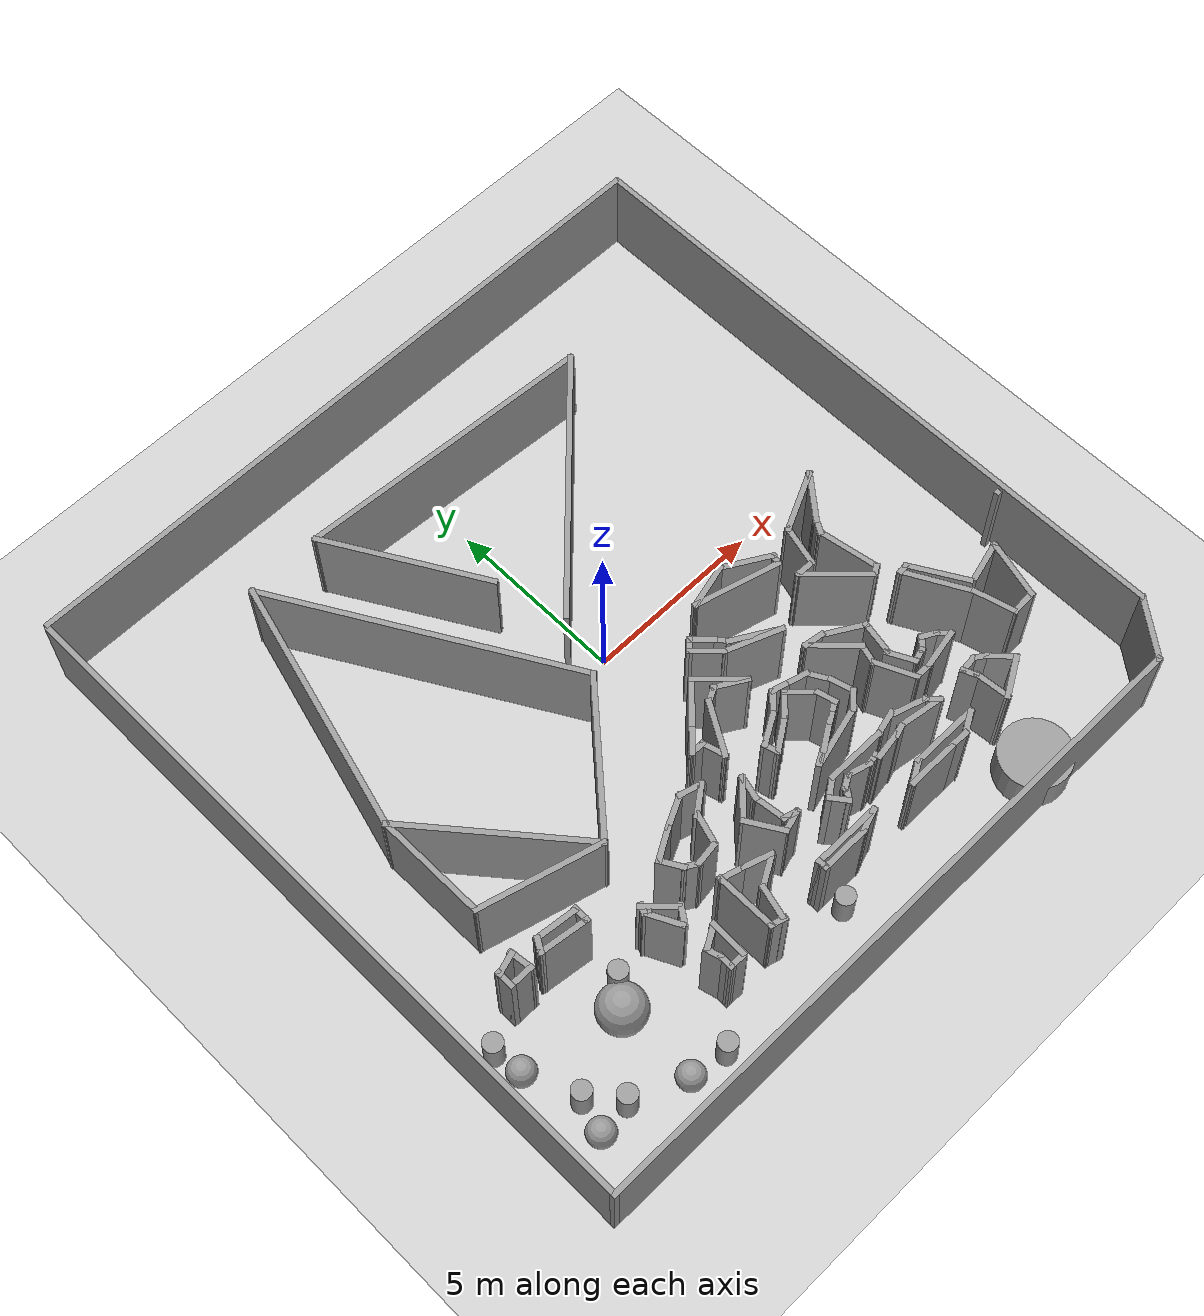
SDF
<sdf version="1.7">
 <world name="default">
  <light name="sun" type="directional">
   <pose>0 0 10 0 -0 0</pose>
   <diffuse>0.8 0.8 0.8 1</diffuse>
   <specular>0.2 0.2 0.2 1</specular>
   <attenuation>
    <range>1000</range>
    <constant>0.9</constant>
    <linear>0.01</linear>
    <quadratic>0.001</quadratic>
   </attenuation>
   <direction>-0.5 0.1 -0.9</direction>
   <spot><inner_angle>0</inner_angle><outer_angle>0</outer_angle><falloff>0</falloff></spot>
  </light>
  <model name="ground_plane">
   <static>1</static>
   <link name="link">
    <collision name="collision">
     <geometry><plane><normal>0 0 1</normal><size>100 100</size></plane></geometry>
     <surface>
      <contact><collide_bitmask>65535</collide_bitmask></contact>
      <friction><ode><mu>100</mu><mu2>50</mu2></ode></friction>
     </surface>
    </collision>
    <visual name="visual">
     <cast_shadows>0</cast_shadows>
     <geometry><plane><normal>0 0 1</normal><size>100 100</size></plane></geometry>
     <material>
      <script><uri>file://media/materials/scripts/gazebo.material</uri><name>Gazebo/Grey</name></script>
     </material>
    </visual>
   </link>
  </model>
  <gravity>0 0 -9.8</gravity>
  <magnetic_field>6e-06 2.3e-05 -4.2e-05</magnetic_field>
  <atmosphere type="adiabatic"/>
  <physics type="ode">
   <max_step_size>0.001</max_step_size>
   <real_time_factor>1</real_time_factor>
   <real_time_update_rate>1000</real_time_update_rate>
  </physics>
  <scene><ambient>0.4 0.4 0.4 1</ambient><background>0.7 0.7 0.7 1</background><shadows>1</shadows></scene>
  <spherical_coordinates>
   <surface_model>EARTH_WGS84</surface_model>
   <latitude_deg>0</latitude_deg>
   <longitude_deg>0</longitude_deg>
   <elevation>0</elevation>
   <heading_deg>0</heading_deg>
  </spherical_coordinates>
  <model name="Untitled">
   <pose>-0.048209 -0.510974 0 0 -0 0</pose>
   <link name="Wall_100">
    <collision name="Wall_100_Collision">
     <geometry><box><size>0.5 0.15 2.5</size></box></geometry>
     <pose>0 0 1.25 0 -0 0</pose>
    </collision>
    <visual name="Wall_100_Visual">
     <pose>0 0 1.25 0 -0 0</pose>
     <geometry><box><size>0.5 0.15 2.5</size></box></geometry>
     <material>
      <script><uri>file://media/materials/scripts/gazebo.material</uri><name>Gazebo/Grey</name></script>
      <ambient>1 1 1 1</ambient>
     </material>
     <meta><layer>0</layer></meta>
    </visual>
    <pose>0.324081 -4.81813 0 0 -0 -1.309</pose>
   </link>
   <link name="Wall_101">
    <collision name="Wall_101_Collision">
     <geometry><box><size>1.11227 0.15 2.5</size></box></geometry>
     <pose>0 0 1.25 0 -0 0</pose>
    </collision>
    <visual name="Wall_101_Visual">
     <pose>0 0 1.25 0 -0 0</pose>
     <geometry><box><size>1.11227 0.15 2.5</size></box></geometry>
     <material>
      <script><uri>file://media/materials/scripts/gazebo.material</uri><name>Gazebo/Grey</name></script>
      <ambient>1 1 1 1</ambient>
     </material>
     <meta><layer>0</layer></meta>
    </visual>
    <pose>0.769787 -4.72041 0 0 -0 0.587686</pose>
   </link>
   <link name="Wall_103">
    <collision name="Wall_103_Collision">
     <geometry><box><size>0.488036 0.15 2.5</size></box></geometry>
     <pose>0 0 1.25 0 -0 0</pose>
    </collision>
    <visual name="Wall_103_Visual">
     <pose>0 0 1.25 0 -0 0</pose>
     <geometry><box><size>0.488036 0.15 2.5</size></box></geometry>
     <material>
      <script><uri>file://media/materials/scripts/gazebo.material</uri><name>Gazebo/Grey</name></script>
      <ambient>1 1 1 1</ambient>
     </material>
     <meta><layer>0</layer></meta>
    </visual>
    <pose>-4.23485 -7.73922 0 0 -0 -1.59502</pose>
   </link>
   <link name="Wall_105">
    <collision name="Wall_105_Collision">
     <geometry><box><size>1.43609 0.15 2.5</size></box></geometry>
     <pose>0 0 1.25 0 -0 0</pose>
    </collision>
    <visual name="Wall_105_Visual">
     <pose>0 0 1.25 0 -0 0</pose>
     <geometry><box><size>1.43609 0.15 2.5</size></box></geometry>
     <material>
      <script><uri>file://media/materials/scripts/gazebo.material</uri><name>Gazebo/Grey</name></script>
      <ambient>1 1 1 1</ambient>
     </material>
     <meta><layer>0</layer></meta>
    </visual>
    <pose>-6.39374 -4.75098 0 0 -0 3.01015</pose>
   </link>
   <link name="Wall_107">
    <collision name="Wall_107_Collision">
     <geometry><box><size>0.75 0.15 2.5</size></box></geometry>
     <pose>0 0 1.25 0 -0 0</pose>
    </collision>
    <visual name="Wall_107_Visual">
     <pose>0 0 1.25 0 -0 0</pose>
     <geometry><box><size>0.75 0.15 2.5</size></box></geometry>
     <material>
      <script><uri>file://media/materials/scripts/gazebo.material</uri><name>Gazebo/Grey</name></script>
      <ambient>1 1 1 1</ambient>
     </material>
     <meta><layer>0</layer></meta>
    </visual>
    <pose>-7.7393 -4.76864 0 0 -0 0</pose>
   </link>
   <link name="Wall_109">
    <collision name="Wall_109_Collision">
     <geometry><box><size>1.0417 0.15 2.5</size></box></geometry>
     <pose>0 0 1.25 0 -0 0</pose>
    </collision>
    <visual name="Wall_109_Visual">
     <pose>0 0 1.25 0 -0 0</pose>
     <geometry><box><size>1.0417 0.15 2.5</size></box></geometry>
     <material>
      <script><uri>file://media/materials/scripts/gazebo.material</uri><name>Gazebo/Grey</name></script>
      <ambient>1 1 1 1</ambient>
     </material>
     <meta><layer>0</layer></meta>
    </visual>
    <pose>-2.47028 -7.52497 0 0 -0 -1.83459</pose>
   </link>
   <link name="Wall_11">
    <collision name="Wall_11_Collision">
     <geometry><box><size>18.5 0.15 2.5</size></box></geometry>
     <pose>0 0 1.25 0 -0 0</pose>
    </collision>
    <visual name="Wall_11_Visual">
     <pose>0 0 1.25 0 -0 0</pose>
     <geometry><box><size>18.5 0.15 2.5</size></box></geometry>
     <material>
      <script><uri>file://media/materials/scripts/gazebo.material</uri><name>Gazebo/Grey</name></script>
      <ambient>1 1 1 1</ambient>
     </material>
     <meta><layer>0</layer></meta>
    </visual>
    <pose>-0.53701 -9.71572 0 0 -0 3.14159</pose>
   </link>
   <link name="Wall_110">
    <collision name="Wall_110_Collision">
     <geometry><box><size>0.5 0.15 2.5</size></box></geometry>
     <pose>0 0 1.25 0 -0 0</pose>
    </collision>
    <visual name="Wall_110_Visual">
     <pose>0 0 1.25 0 -0 0</pose>
     <geometry><box><size>0.5 0.15 2.5</size></box></geometry>
     <material>
      <script><uri>file://media/materials/scripts/gazebo.material</uri><name>Gazebo/Grey</name></script>
      <ambient>1 1 1 1</ambient>
     </material>
     <meta><layer>0</layer></meta>
    </visual>
    <pose>-2.72574 -7.9101 0 0 -0 2.87979</pose>
   </link>
   <link name="Wall_111">
    <collision name="Wall_111_Collision">
     <geometry><box><size>1.76019 0.15 2.5</size></box></geometry>
     <pose>0 0 1.25 0 -0 0</pose>
    </collision>
    <visual name="Wall_111_Visual">
     <pose>0 0 1.25 0 -0 0</pose>
     <geometry><box><size>1.76019 0.15 2.5</size></box></geometry>
     <material>
      <script><uri>file://media/materials/scripts/gazebo.material</uri><name>Gazebo/Grey</name></script>
      <ambient>1 1 1 1</ambient>
     </material>
     <meta><layer>0</layer></meta>
    </visual>
    <pose>-2.89443 -7.05971 0 0 -0 1.57037</pose>
   </link>
   <link name="Wall_113">
    <collision name="Wall_113_Collision">
     <geometry><box><size>1 0.15 2.5</size></box></geometry>
     <pose>0 0 1.25 0 -0 0</pose>
    </collision>
    <visual name="Wall_113_Visual">
     <pose>0 0 1.25 0 -0 0</pose>
     <geometry><box><size>1 0.15 2.5</size></box></geometry>
     <material>
      <script><uri>file://media/materials/scripts/gazebo.material</uri><name>Gazebo/Grey</name></script>
      <ambient>1 1 1 1</ambient>
     </material>
     <meta><layer>0</layer></meta>
    </visual>
    <pose>-1.98596 -6.88204 0 0 -0 -2.61799</pose>
   </link>
   <link name="Wall_12">
    <collision name="Wall_12_Collision">
     <geometry><box><size>19.5 0.15 2.5</size></box></geometry>
     <pose>0 0 1.25 0 -0 0</pose>
    </collision>
    <visual name="Wall_12_Visual">
     <pose>0 0 1.25 0 -0 0</pose>
     <geometry><box><size>19.5 0.15 2.5</size></box></geometry>
     <material>
      <script><uri>file://media/materials/scripts/gazebo.material</uri><name>Gazebo/Grey</name></script>
      <ambient>1 1 1 1</ambient>
     </material>
     <meta><layer>0</layer></meta>
    </visual>
    <pose>-9.71201 -0.040722 0 0 -0 1.5708</pose>
   </link>
   <link name="Wall_120">
    <collision name="Wall_120_Collision">
     <geometry><box><size>0.25 0.15 2.5</size></box></geometry>
     <pose>0 0 1.25 0 -0 0</pose>
    </collision>
    <visual name="Wall_120_Visual">
     <pose>0 0 1.25 0 -0 0</pose>
     <geometry><box><size>0.25 0.15 2.5</size></box></geometry>
     <material>
      <script><uri>file://media/materials/scripts/gazebo.material</uri><name>Gazebo/Grey</name></script>
      <ambient>1 1 1 1</ambient>
     </material>
     <meta><layer>0</layer></meta>
    </visual>
    <pose>-0.982432 -7.71789 0 0 -0 1.5708</pose>
   </link>
   <link name="Wall_121">
    <collision name="Wall_121_Collision">
     <geometry><box><size>0.25 0.15 2.5</size></box></geometry>
     <pose>0 0 1.25 0 -0 0</pose>
    </collision>
    <visual name="Wall_121_Visual">
     <pose>0 0 1.25 0 -0 0</pose>
     <geometry><box><size>0.25 0.15 2.5</size></box></geometry>
     <material>
      <script><uri>file://media/materials/scripts/gazebo.material</uri><name>Gazebo/Grey</name></script>
      <ambient>1 1 1 1</ambient>
     </material>
     <meta><layer>0</layer></meta>
    </visual>
    <pose>-0.982432 -7.61789 0 0 -0 1.5708</pose>
   </link>
   <link name="Wall_122">
    <collision name="Wall_122_Collision">
     <geometry><box><size>2 0.15 2.5</size></box></geometry>
     <pose>0 0 1.25 0 -0 0</pose>
    </collision>
    <visual name="Wall_122_Visual">
     <pose>0 0 1.25 0 -0 0</pose>
     <geometry><box><size>2 0.15 2.5</size></box></geometry>
     <material>
      <script><uri>file://media/materials/scripts/gazebo.material</uri><name>Gazebo/Grey</name></script>
      <ambient>1 1 1 1</ambient>
     </material>
     <meta><layer>0</layer></meta>
    </visual>
    <pose>-0.057432 -7.56789 0 0 -0 0</pose>
   </link>
   <link name="Wall_123">
    <collision name="Wall_123_Collision">
     <geometry><box><size>0.753289 0.15 2.5</size></box></geometry>
     <pose>0 0 1.25 0 -0 0</pose>
    </collision>
    <visual name="Wall_123_Visual">
     <pose>0 0 1.25 0 -0 0</pose>
     <geometry><box><size>0.753289 0.15 2.5</size></box></geometry>
     <material>
      <script><uri>file://media/materials/scripts/gazebo.material</uri><name>Gazebo/Grey</name></script>
      <ambient>1 1 1 1</ambient>
     </material>
     <meta><layer>0</layer></meta>
    </visual>
    <pose>0.582982 -7.66789 0 0 -0 -2.80368</pose>
   </link>
   <link name="Wall_125">
    <collision name="Wall_125_Collision">
     <geometry><box><size>0.75 0.15 2.5</size></box></geometry>
     <pose>0 0 1.25 0 -0 0</pose>
    </collision>
    <visual name="Wall_125_Visual">
     <pose>0 0 1.25 0 -0 0</pose>
     <geometry><box><size>0.75 0.15 2.5</size></box></geometry>
     <material>
      <script><uri>file://media/materials/scripts/gazebo.material</uri><name>Gazebo/Grey</name></script>
      <ambient>1 1 1 1</ambient>
     </material>
     <meta><layer>0</layer></meta>
    </visual>
    <pose>2.27315 -7.61311 0 0 -0 0.523599</pose>
   </link>
   <link name="Wall_126">
    <collision name="Wall_126_Collision">
     <geometry><box><size>2 0.15 2.5</size></box></geometry>
     <pose>0 0 1.25 0 -0 0</pose>
    </collision>
    <visual name="Wall_126_Visual">
     <pose>0 0 1.25 0 -0 0</pose>
     <geometry><box><size>2 0.15 2.5</size></box></geometry>
     <material>
      <script><uri>file://media/materials/scripts/gazebo.material</uri><name>Gazebo/Grey</name></script>
      <ambient>1 1 1 1</ambient>
     </material>
     <meta><layer>0</layer></meta>
    </visual>
    <pose>3.45796 -7.46311 0 0 -0 0</pose>
   </link>
   <link name="Wall_127">
    <collision name="Wall_127_Collision">
     <geometry><box><size>0.75 0.15 2.5</size></box></geometry>
     <pose>0 0 1.25 0 -0 0</pose>
    </collision>
    <visual name="Wall_127_Visual">
     <pose>0 0 1.25 0 -0 0</pose>
     <geometry><box><size>0.75 0.15 2.5</size></box></geometry>
     <material>
      <script><uri>file://media/materials/scripts/gazebo.material</uri><name>Gazebo/Grey</name></script>
      <ambient>1 1 1 1</ambient>
     </material>
     <meta><layer>0</layer></meta>
    </visual>
    <pose>4.12315 -7.61311 0 0 -0 -2.61799</pose>
   </link>
   <link name="Wall_128">
    <collision name="Wall_128_Collision">
     <geometry><box><size>0.65 0.15 2.5</size></box></geometry>
     <pose>0 0 1.25 0 -0 0</pose>
    </collision>
    <visual name="Wall_128_Visual">
     <pose>0 0 1.25 0 -0 0</pose>
     <geometry><box><size>0.65 0.15 2.5</size></box></geometry>
     <material>
      <script><uri>file://media/materials/scripts/gazebo.material</uri><name>Gazebo/Grey</name></script>
      <ambient>1 1 1 1</ambient>
     </material>
     <meta><layer>0</layer></meta>
    </visual>
    <pose>3.61334 -7.76311 0 0 -0 3.14159</pose>
   </link>
   <link name="Wall_130">
    <collision name="Wall_130_Collision">
     <geometry><box><size>0.649842 0.15 2.5</size></box></geometry>
     <pose>0 0 1.25 0 -0 0</pose>
    </collision>
    <visual name="Wall_130_Visual">
     <pose>0 0 1.25 0 -0 0</pose>
     <geometry><box><size>0.649842 0.15 2.5</size></box></geometry>
     <material>
      <script><uri>file://media/materials/scripts/gazebo.material</uri><name>Gazebo/Grey</name></script>
      <ambient>1 1 1 1</ambient>
     </material>
     <meta><layer>0</layer></meta>
    </visual>
    <pose>3.14663 -3.54986 0 0 -0 2.99528</pose>
   </link>
   <link name="Wall_131">
    <collision name="Wall_131_Collision">
     <geometry><box><size>1.5 0.15 2.5</size></box></geometry>
     <pose>0 0 1.25 0 -0 0</pose>
    </collision>
    <visual name="Wall_131_Visual">
     <pose>0 0 1.25 0 -0 0</pose>
     <geometry><box><size>1.5 0.15 2.5</size></box></geometry>
     <material>
      <script><uri>file://media/materials/scripts/gazebo.material</uri><name>Gazebo/Grey</name></script>
      <ambient>1 1 1 1</ambient>
     </material>
     <meta><layer>0</layer></meta>
    </visual>
    <pose>3.37668 -3.99072 0 0 -0 -0.785398</pose>
   </link>
   <link name="Wall_132">
    <collision name="Wall_132_Collision">
     <geometry><box><size>0.68894 0.15 2.5</size></box></geometry>
     <pose>0 0 1.25 0 -0 0</pose>
    </collision>
    <visual name="Wall_132_Visual">
     <pose>0 0 1.25 0 -0 0</pose>
     <geometry><box><size>0.68894 0.15 2.5</size></box></geometry>
     <material>
      <script><uri>file://media/materials/scripts/gazebo.material</uri><name>Gazebo/Grey</name></script>
      <ambient>1 1 1 1</ambient>
     </material>
     <meta><layer>0</layer></meta>
    </visual>
    <pose>3.7809 -4.71434 0 0 -0 -1.84544</pose>
   </link>
   <link name="Wall_133">
    <collision name="Wall_133_Collision">
     <geometry><box><size>1.23729 0.15 2.5</size></box></geometry>
     <pose>0 0 1.25 0 -0 0</pose>
    </collision>
    <visual name="Wall_133_Visual">
     <pose>0 0 1.25 0 -0 0</pose>
     <geometry><box><size>1.23729 0.15 2.5</size></box></geometry>
     <material>
      <script><uri>file://media/materials/scripts/gazebo.material</uri><name>Gazebo/Grey</name></script>
      <ambient>1 1 1 1</ambient>
     </material>
     <meta><layer>0</layer></meta>
    </visual>
    <pose>3.94368 -5.46959 0 0 -0 -1.14848</pose>
   </link>
   <link name="Wall_134">
    <collision name="Wall_134_Collision">
     <geometry><box><size>0.589498 0.15 2.5</size></box></geometry>
     <pose>0 0 1.25 0 -0 0</pose>
    </collision>
    <visual name="Wall_134_Visual">
     <pose>0 0 1.25 0 -0 0</pose>
     <geometry><box><size>0.589498 0.15 2.5</size></box></geometry>
     <material>
      <script><uri>file://media/materials/scripts/gazebo.material</uri><name>Gazebo/Grey</name></script>
      <ambient>1 1 1 1</ambient>
     </material>
     <meta><layer>0</layer></meta>
    </visual>
    <pose>4.38622 -5.96132 0 0 -0 0.018896</pose>
   </link>
   <link name="Wall_135">
    <collision name="Wall_135_Collision">
     <geometry><box><size>1.19695 0.15 2.5</size></box></geometry>
     <pose>0 0 1.25 0 -0 0</pose>
    </collision>
    <visual name="Wall_135_Visual">
     <pose>0 0 1.25 0 -0 0</pose>
     <geometry><box><size>1.19695 0.15 2.5</size></box></geometry>
     <material>
      <script><uri>file://media/materials/scripts/gazebo.material</uri><name>Gazebo/Grey</name></script>
      <ambient>1 1 1 1</ambient>
     </material>
     <meta><layer>0</layer></meta>
    </visual>
    <pose>5.11922 -5.85438 0 0 -0 0.197635</pose>
   </link>
   <link name="Wall_136">
    <collision name="Wall_136_Collision">
     <geometry><box><size>0.5 0.15 2.5</size></box></geometry>
     <pose>0 0 1.25 0 -0 0</pose>
    </collision>
    <visual name="Wall_136_Visual">
     <pose>0 0 1.25 0 -0 0</pose>
     <geometry><box><size>0.5 0.15 2.5</size></box></geometry>
     <material>
      <script><uri>file://media/materials/scripts/gazebo.material</uri><name>Gazebo/Grey</name></script>
      <ambient>1 1 1 1</ambient>
     </material>
     <meta><layer>0</layer></meta>
    </visual>
    <pose>5.50876 -5.62785 0 0 -0 2.35619</pose>
   </link>
   <link name="Wall_138">
    <collision name="Wall_138_Collision">
     <geometry><box><size>0.15 0.15 2.5</size></box></geometry>
     <pose>0 0 1.25 0 -0 0</pose>
    </collision>
    <visual name="Wall_138_Visual">
     <pose>0 0 1.25 0 -0 0</pose>
     <geometry><box><size>0.15 0.15 2.5</size></box></geometry>
     <material>
      <script><uri>file://media/materials/scripts/gazebo.material</uri><name>Gazebo/Grey</name></script>
      <ambient>1 1 1 1</ambient>
     </material>
     <meta><layer>0</layer></meta>
    </visual>
    <pose>4.45791 -5.65408 0 0 -0 0</pose>
   </link>
   <link name="Wall_14">
    <collision name="Wall_14_Collision">
     <geometry><box><size>1.5 0.15 2.5</size></box></geometry>
     <pose>0 0 1.25 0 -0 0</pose>
    </collision>
    <visual name="Wall_14_Visual">
     <pose>0 0 1.25 0 -0 0</pose>
     <geometry><box><size>1.5 0.15 2.5</size></box></geometry>
     <material>
      <script><uri>file://media/materials/scripts/gazebo.material</uri><name>Gazebo/Grey</name></script>
      <ambient>1 1 1 1</ambient>
     </material>
     <meta><layer>0</layer></meta>
    </visual>
    <pose>2.68834 -7.76311 0 0 -0 0</pose>
   </link>
   <link name="Wall_140">
    <collision name="Wall_140_Collision">
     <geometry><box><size>0.45593 0.15 2.5</size></box></geometry>
     <pose>0 0 1.25 0 -0 0</pose>
    </collision>
    <visual name="Wall_140_Visual">
     <pose>0 0 1.25 0 -0 0</pose>
     <geometry><box><size>0.45593 0.15 2.5</size></box></geometry>
     <material>
      <script><uri>file://media/materials/scripts/gazebo.material</uri><name>Gazebo/Grey</name></script>
      <ambient>1 1 1 1</ambient>
     </material>
     <meta><layer>0</layer></meta>
    </visual>
    <pose>5.64164 -6.67189 0 0 -0 2.53262</pose>
   </link>
   <link name="Wall_145">
    <collision name="Wall_145_Collision">
     <geometry><box><size>0.542134 0.15 2.5</size></box></geometry>
     <pose>0 0 1.25 0 -0 0</pose>
    </collision>
    <visual name="Wall_145_Visual">
     <pose>0 0 1.25 0 -0 0</pose>
     <geometry><box><size>0.542134 0.15 2.5</size></box></geometry>
     <material>
      <script><uri>file://media/materials/scripts/gazebo.material</uri><name>Gazebo/Grey</name></script>
      <ambient>1 1 1 1</ambient>
     </material>
     <meta><layer>0</layer></meta>
    </visual>
    <pose>5.29497 -6.6036 0 0 -0 -3.04348</pose>
   </link>
   <link name="Wall_146">
    <collision name="Wall_146_Collision">
     <geometry><box><size>0.477049 0.15 2.5</size></box></geometry>
     <pose>0 0 1.25 0 -0 0</pose>
    </collision>
    <visual name="Wall_146_Visual">
     <pose>0 0 1.25 0 -0 0</pose>
     <geometry><box><size>0.477049 0.15 2.5</size></box></geometry>
     <material>
      <script><uri>file://media/materials/scripts/gazebo.material</uri><name>Gazebo/Grey</name></script>
      <ambient>1 1 1 1</ambient>
     </material>
     <meta><layer>0</layer></meta>
    </visual>
    <pose>5.13517 -6.77435 0 0 -0 -1.1858</pose>
   </link>
   <link name="Wall_147">
    <collision name="Wall_147_Collision">
     <geometry><box><size>1.05556 0.15 2.5</size></box></geometry>
     <pose>0 0 1.25 0 -0 0</pose>
    </collision>
    <visual name="Wall_147_Visual">
     <pose>0 0 1.25 0 -0 0</pose>
     <geometry><box><size>1.05556 0.15 2.5</size></box></geometry>
     <material>
      <script><uri>file://media/materials/scripts/gazebo.material</uri><name>Gazebo/Grey</name></script>
      <ambient>1 1 1 1</ambient>
     </material>
     <meta><layer>0</layer></meta>
    </visual>
    <pose>5.2618 -7.377 0 0 -0 -1.48427</pose>
   </link>
   <link name="Wall_148">
    <collision name="Wall_148_Collision">
     <geometry><box><size>1.25 0.15 2.5</size></box></geometry>
     <pose>0 0 1.25 0 -0 0</pose>
    </collision>
    <visual name="Wall_148_Visual">
     <pose>0 0 1.25 0 -0 0</pose>
     <geometry><box><size>1.25 0.15 2.5</size></box></geometry>
     <material>
      <script><uri>file://media/materials/scripts/gazebo.material</uri><name>Gazebo/Grey</name></script>
      <ambient>1 1 1 1</ambient>
     </material>
     <meta><layer>0</layer></meta>
    </visual>
    <pose>5.77724 -7.55308 0 0 -0 0.523599</pose>
   </link>
   <link name="Wall_150">
    <collision name="Wall_150_Collision">
     <geometry><box><size>1.68602 0.15 2.5</size></box></geometry>
     <pose>0 0 1.25 0 -0 0</pose>
    </collision>
    <visual name="Wall_150_Visual">
     <pose>0 0 1.25 0 -0 0</pose>
     <geometry><box><size>1.68602 0.15 2.5</size></box></geometry>
     <material>
      <script><uri>file://media/materials/scripts/gazebo.material</uri><name>Gazebo/Grey</name></script>
      <ambient>1 1 1 1</ambient>
     </material>
     <meta><layer>0</layer></meta>
    </visual>
    <pose>2.11857 -2.53024 0 0 -0 2.77294</pose>
   </link>
   <link name="Wall_152">
    <collision name="Wall_152_Collision">
     <geometry><box><size>1.5 0.15 2.5</size></box></geometry>
     <pose>0 0 1.25 0 -0 0</pose>
    </collision>
    <visual name="Wall_152_Visual">
     <pose>0 0 1.25 0 -0 0</pose>
     <geometry><box><size>1.5 0.15 2.5</size></box></geometry>
     <material>
      <script><uri>file://media/materials/scripts/gazebo.material</uri><name>Gazebo/Grey</name></script>
      <ambient>1 1 1 1</ambient>
     </material>
     <meta><layer>0</layer></meta>
    </visual>
    <pose>2.25041 -2.4695 0 0 -0 -0.523599</pose>
   </link>
   <link name="Wall_154">
    <collision name="Wall_154_Collision">
     <geometry><box><size>1.60803 0.15 2.5</size></box></geometry>
     <pose>0 0 1.25 0 -0 0</pose>
    </collision>
    <visual name="Wall_154_Visual">
     <pose>0 0 1.25 0 -0 0</pose>
     <geometry><box><size>1.60803 0.15 2.5</size></box></geometry>
     <material>
      <script><uri>file://media/materials/scripts/gazebo.material</uri><name>Gazebo/Grey</name></script>
      <ambient>1 1 1 1</ambient>
     </material>
     <meta><layer>0</layer></meta>
    </visual>
    <pose>-0.202375 -3.54716 0 0 -0 1.03535</pose>
   </link>
   <link name="Wall_155">
    <collision name="Wall_155_Collision">
     <geometry><box><size>0.50965 0.15 2.5</size></box></geometry>
     <pose>0 0 1.25 0 -0 0</pose>
    </collision>
    <visual name="Wall_155_Visual">
     <pose>0 0 1.25 0 -0 0</pose>
     <geometry><box><size>0.50965 0.15 2.5</size></box></geometry>
     <material>
      <script><uri>file://media/materials/scripts/gazebo.material</uri><name>Gazebo/Grey</name></script>
      <ambient>1 1 1 1</ambient>
     </material>
     <meta><layer>0</layer></meta>
    </visual>
    <pose>0.360562 -2.83275 0 0 -0 0.50772</pose>
   </link>
   <link name="Wall_157">
    <collision name="Wall_157_Collision">
     <geometry><box><size>1.25 0.15 2.5</size></box></geometry>
     <pose>0 0 1.25 0 -0 0</pose>
    </collision>
    <visual name="Wall_157_Visual">
     <pose>0 0 1.25 0 -0 0</pose>
     <geometry><box><size>1.25 0.15 2.5</size></box></geometry>
     <material>
      <script><uri>file://media/materials/scripts/gazebo.material</uri><name>Gazebo/Grey</name></script>
      <ambient>1 1 1 1</ambient>
     </material>
     <meta><layer>0</layer></meta>
    </visual>
    <pose>-1.09648 -5.24869 0 0 -0 -2.35619</pose>
   </link>
   <link name="Wall_158">
    <collision name="Wall_158_Collision">
     <geometry><box><size>1.16438 0.15 2.5</size></box></geometry>
     <pose>0 0 1.25 0 -0 0</pose>
    </collision>
    <visual name="Wall_158_Visual">
     <pose>0 0 1.25 0 -0 0</pose>
     <geometry><box><size>1.16438 0.15 2.5</size></box></geometry>
     <material>
      <script><uri>file://media/materials/scripts/gazebo.material</uri><name>Gazebo/Grey</name></script>
      <ambient>1 1 1 1</ambient>
     </material>
     <meta><layer>0</layer></meta>
    </visual>
    <pose>-1.22348 -6.07192 0 0 -0 -1.02814</pose>
   </link>
   <link name="Wall_159">
    <collision name="Wall_159_Collision">
     <geometry><box><size>0.692591 0.15 2.5</size></box></geometry>
     <pose>0 0 1.25 0 -0 0</pose>
    </collision>
    <visual name="Wall_159_Visual">
     <pose>0 0 1.25 0 -0 0</pose>
     <geometry><box><size>0.692591 0.15 2.5</size></box></geometry>
     <material>
      <script><uri>file://media/materials/scripts/gazebo.material</uri><name>Gazebo/Grey</name></script>
      <ambient>1 1 1 1</ambient>
     </material>
     <meta><layer>0</layer></meta>
    </visual>
    <pose>-0.694153 -6.4286 0 0 -0 0.290262</pose>
   </link>
   <link name="Wall_160">
    <collision name="Wall_160_Collision">
     <geometry><box><size>0.5 0.15 2.5</size></box></geometry>
     <pose>0 0 1.25 0 -0 0</pose>
    </collision>
    <visual name="Wall_160_Visual">
     <pose>0 0 1.25 0 -0 0</pose>
     <geometry><box><size>0.5 0.15 2.5</size></box></geometry>
     <material>
      <script><uri>file://media/materials/scripts/gazebo.material</uri><name>Gazebo/Grey</name></script>
      <ambient>1 1 1 1</ambient>
     </material>
     <meta><layer>0</layer></meta>
    </visual>
    <pose>-0.603243 -6.30566 0 0 -0 2.87979</pose>
   </link>
   <link name="Wall_161">
    <collision name="Wall_161_Collision">
     <geometry><box><size>0.976019 0.15 2.5</size></box></geometry>
     <pose>0 0 1.25 0 -0 0</pose>
    </collision>
    <visual name="Wall_161_Visual">
     <pose>0 0 1.25 0 -0 0</pose>
     <geometry><box><size>0.976019 0.15 2.5</size></box></geometry>
     <material>
      <script><uri>file://media/materials/scripts/gazebo.material</uri><name>Gazebo/Grey</name></script>
      <ambient>1 1 1 1</ambient>
     </material>
     <meta><layer>0</layer></meta>
    </visual>
    <pose>-0.817573 -5.84985 0 0 -0 1.68068</pose>
   </link>
   <link name="Wall_162">
    <collision name="Wall_162_Collision">
     <geometry><box><size>0.75 0.15 2.5</size></box></geometry>
     <pose>0 0 1.25 0 -0 0</pose>
    </collision>
    <visual name="Wall_162_Visual">
     <pose>0 0 1.25 0 -0 0</pose>
     <geometry><box><size>0.75 0.15 2.5</size></box></geometry>
     <material>
      <script><uri>file://media/materials/scripts/gazebo.material</uri><name>Gazebo/Grey</name></script>
      <ambient>1 1 1 1</ambient>
     </material>
     <meta><layer>0</layer></meta>
    </visual>
    <pose>-0.785221 -5.14955 0 0 -0 1.309</pose>
   </link>
   <link name="Wall_164">
    <collision name="Wall_164_Collision">
     <geometry><box><size>0.611635 0.15 2.5</size></box></geometry>
     <pose>0 0 1.25 0 -0 0</pose>
    </collision>
    <visual name="Wall_164_Visual">
     <pose>0 0 1.25 0 -0 0</pose>
     <geometry><box><size>0.611635 0.15 2.5</size></box></geometry>
     <material>
      <script><uri>file://media/materials/scripts/gazebo.material</uri><name>Gazebo/Grey</name></script>
      <ambient>1 1 1 1</ambient>
     </material>
     <meta><layer>0</layer></meta>
    </visual>
    <pose>0.490586 -6.82526 0 0 -0 -0.928742</pose>
   </link>
   <link name="Wall_165">
    <collision name="Wall_165_Collision">
     <geometry><box><size>0.385134 0.15 2.5</size></box></geometry>
     <pose>0 0 1.25 0 -0 0</pose>
    </collision>
    <visual name="Wall_165_Visual">
     <pose>0 0 1.25 0 -0 0</pose>
     <geometry><box><size>0.385134 0.15 2.5</size></box></geometry>
     <material>
      <script><uri>file://media/materials/scripts/gazebo.material</uri><name>Gazebo/Grey</name></script>
      <ambient>1 1 1 1</ambient>
     </material>
     <meta><layer>0</layer></meta>
    </visual>
    <pose>0.691599 -6.91768 0 0 -0 0.904641</pose>
   </link>
   <link name="Wall_166">
    <collision name="Wall_166_Collision">
     <geometry><box><size>0.25 0.15 2.5</size></box></geometry>
     <pose>0 0 1.25 0 -0 0</pose>
    </collision>
    <visual name="Wall_166_Visual">
     <pose>0 0 1.25 0 -0 0</pose>
     <geometry><box><size>0.25 0.15 2.5</size></box></geometry>
     <material>
      <script><uri>file://media/materials/scripts/gazebo.material</uri><name>Gazebo/Grey</name></script>
      <ambient>1 1 1 1</ambient>
     </material>
     <meta><layer>0</layer></meta>
    </visual>
    <pose>0.777192 -6.77696 0 0 -0 1.309</pose>
   </link>
   <link name="Wall_167">
    <collision name="Wall_167_Collision">
     <geometry><box><size>0.5 0.15 2.5</size></box></geometry>
     <pose>0 0 1.25 0 -0 0</pose>
    </collision>
    <visual name="Wall_167_Visual">
     <pose>0 0 1.25 0 -0 0</pose>
     <geometry><box><size>0.5 0.15 2.5</size></box></geometry>
     <material>
      <script><uri>file://media/materials/scripts/gazebo.material</uri><name>Gazebo/Grey</name></script>
      <ambient>1 1 1 1</ambient>
     </material>
     <meta><layer>0</layer></meta>
    </visual>
    <pose>0.941688 -6.64116 0 0 -0 0.523599</pose>
   </link>
   <link name="Wall_168">
    <collision name="Wall_168_Collision">
     <geometry><box><size>0.75 0.15 2.5</size></box></geometry>
     <pose>0 0 1.25 0 -0 0</pose>
    </collision>
    <visual name="Wall_168_Visual">
     <pose>0 0 1.25 0 -0 0</pose>
     <geometry><box><size>0.75 0.15 2.5</size></box></geometry>
     <material>
      <script><uri>file://media/materials/scripts/gazebo.material</uri><name>Gazebo/Grey</name></script>
      <ambient>1 1 1 1</ambient>
     </material>
     <meta><layer>0</layer></meta>
    </visual>
    <pose>1.38302 -6.63131 0 0 -0 -0.261799</pose>
   </link>
   <link name="Wall_169">
    <collision name="Wall_169_Collision">
     <geometry><box><size>0.426039 0.15 2.5</size></box></geometry>
     <pose>0 0 1.25 0 -0 0</pose>
    </collision>
    <visual name="Wall_169_Visual">
     <pose>0 0 1.25 0 -0 0</pose>
     <geometry><box><size>0.426039 0.15 2.5</size></box></geometry>
     <material>
      <script><uri>file://media/materials/scripts/gazebo.material</uri><name>Gazebo/Grey</name></script>
      <ambient>1 1 1 1</ambient>
     </material>
     <meta><layer>0</layer></meta>
    </visual>
    <pose>1.80802 -6.6813 0 0 -0 0.201667</pose>
   </link>
   <link name="Wall_170">
    <collision name="Wall_170_Collision">
     <geometry><box><size>0.25 0.15 2.5</size></box></geometry>
     <pose>0 0 1.25 0 -0 0</pose>
    </collision>
    <visual name="Wall_170_Visual">
     <pose>0 0 1.25 0 -0 0</pose>
     <geometry><box><size>0.25 0.15 2.5</size></box></geometry>
     <material>
      <script><uri>file://media/materials/scripts/gazebo.material</uri><name>Gazebo/Grey</name></script>
      <ambient>1 1 1 1</ambient>
     </material>
     <meta><layer>0</layer></meta>
    </visual>
    <pose>1.95618 -6.70195 0 0 -0 -1.309</pose>
   </link>
   <link name="Wall_171">
    <collision name="Wall_171_Collision">
     <geometry><box><size>0.854898 0.15 2.5</size></box></geometry>
     <pose>0 0 1.25 0 -0 0</pose>
    </collision>
    <visual name="Wall_171_Visual">
     <pose>0 0 1.25 0 -0 0</pose>
     <geometry><box><size>0.854898 0.15 2.5</size></box></geometry>
     <material>
      <script><uri>file://media/materials/scripts/gazebo.material</uri><name>Gazebo/Grey</name></script>
      <ambient>1 1 1 1</ambient>
     </material>
     <meta><layer>0</layer></meta>
    </visual>
    <pose>2.3176 -6.69746 0 0 -0 0.150344</pose>
   </link>
   <link name="Wall_172">
    <collision name="Wall_172_Collision">
     <geometry><box><size>0.416595 0.15 2.5</size></box></geometry>
     <pose>0 0 1.25 0 -0 0</pose>
    </collision>
    <visual name="Wall_172_Visual">
     <pose>0 0 1.25 0 -0 0</pose>
     <geometry><box><size>0.416595 0.15 2.5</size></box></geometry>
     <material>
      <script><uri>file://media/materials/scripts/gazebo.material</uri><name>Gazebo/Grey</name></script>
      <ambient>1 1 1 1</ambient>
     </material>
     <meta><layer>0</layer></meta>
    </visual>
    <pose>2.79296 -6.61689 0 0 -0 0.31126</pose>
   </link>
   <link name="Wall_174">
    <collision name="Wall_174_Collision">
     <geometry><box><size>0.5 0.15 2.5</size></box></geometry>
     <pose>0 0 1.25 0 -0 0</pose>
    </collision>
    <visual name="Wall_174_Visual">
     <pose>0 0 1.25 0 -0 0</pose>
     <geometry><box><size>0.5 0.15 2.5</size></box></geometry>
     <material>
      <script><uri>file://media/materials/scripts/gazebo.material</uri><name>Gazebo/Grey</name></script>
      <ambient>1 1 1 1</ambient>
     </material>
     <meta><layer>0</layer></meta>
    </visual>
    <pose>1.82667 -5.29631 0 0 -0 -2.61799</pose>
   </link>
   <link name="Wall_178">
    <collision name="Wall_178_Collision">
     <geometry><box><size>0.5 0.15 2.5</size></box></geometry>
     <pose>0 0 1.25 0 -0 0</pose>
    </collision>
    <visual name="Wall_178_Visual">
     <pose>0 0 1.25 0 -0 0</pose>
     <geometry><box><size>0.5 0.15 2.5</size></box></geometry>
     <material>
      <script><uri>file://media/materials/scripts/gazebo.material</uri><name>Gazebo/Grey</name></script>
      <ambient>1 1 1 1</ambient>
     </material>
     <meta><layer>0</layer></meta>
    </visual>
    <pose>2.12978 -5.12131 0 0 -0 0.523599</pose>
   </link>
   <link name="Wall_179">
    <collision name="Wall_179_Collision">
     <geometry><box><size>0.626539 0.15 2.5</size></box></geometry>
     <pose>0 0 1.25 0 -0 0</pose>
    </collision>
    <visual name="Wall_179_Visual">
     <pose>0 0 1.25 0 -0 0</pose>
     <geometry><box><size>0.626539 0.15 2.5</size></box></geometry>
     <material>
      <script><uri>file://media/materials/scripts/gazebo.material</uri><name>Gazebo/Grey</name></script>
      <ambient>1 1 1 1</ambient>
     </material>
     <meta><layer>0</layer></meta>
    </visual>
    <pose>2.23629 -4.80273 0 0 -0 1.81704</pose>
   </link>
   <link name="Wall_180">
    <collision name="Wall_180_Collision">
     <geometry><box><size>0.946243 0.15 2.5</size></box></geometry>
     <pose>0 0 1.25 0 -0 0</pose>
    </collision>
    <visual name="Wall_180_Visual">
     <pose>0 0 1.25 0 -0 0</pose>
     <geometry><box><size>0.946243 0.15 2.5</size></box></geometry>
     <material>
      <script><uri>file://media/materials/scripts/gazebo.material</uri><name>Gazebo/Grey</name></script>
      <ambient>1 1 1 1</ambient>
     </material>
     <meta><layer>0</layer></meta>
    </visual>
    <pose>1.89423 -4.29263 0 0 -0 2.36501</pose>
   </link>
   <link name="Wall_182">
    <collision name="Wall_182_Collision">
     <geometry><box><size>0.773513 0.15 2.5</size></box></geometry>
     <pose>0 0 1.25 0 -0 0</pose>
    </collision>
    <visual name="Wall_182_Visual">
     <pose>0 0 1.25 0 -0 0</pose>
     <geometry><box><size>0.773513 0.15 2.5</size></box></geometry>
     <material>
      <script><uri>file://media/materials/scripts/gazebo.material</uri><name>Gazebo/Grey</name></script>
      <ambient>1 1 1 1</ambient>
     </material>
     <meta><layer>0</layer></meta>
    </visual>
    <pose>1.41236 -5.5516 0 0 -0 -2.5733</pose>
   </link>
   <link name="Wall_183">
    <collision name="Wall_183_Collision">
     <geometry><box><size>0.5 0.15 2.5</size></box></geometry>
     <pose>0 0 1.25 0 -0 0</pose>
    </collision>
    <visual name="Wall_183_Visual">
     <pose>0 0 1.25 0 -0 0</pose>
     <geometry><box><size>0.5 0.15 2.5</size></box></geometry>
     <material>
      <script><uri>file://media/materials/scripts/gazebo.material</uri><name>Gazebo/Grey</name></script>
      <ambient>1 1 1 1</ambient>
     </material>
     <meta><layer>0</layer></meta>
    </visual>
    <pose>0.971964 -5.79384 0 0 -0 -2.61799</pose>
   </link>
   <link name="Wall_184">
    <collision name="Wall_184_Collision">
     <geometry><box><size>1.82264 0.15 2.5</size></box></geometry>
     <pose>0 0 1.25 0 -0 0</pose>
    </collision>
    <visual name="Wall_184_Visual">
     <pose>0 0 1.25 0 -0 0</pose>
     <geometry><box><size>1.82264 0.15 2.5</size></box></geometry>
     <material>
      <script><uri>file://media/materials/scripts/gazebo.material</uri><name>Gazebo/Grey</name></script>
      <ambient>1 1 1 1</ambient>
     </material>
     <meta><layer>0</layer></meta>
    </visual>
    <pose>1.65502 -5.68055 0 0 -0 0.258555</pose>
   </link>
   <link name="Wall_185">
    <collision name="Wall_185_Collision">
     <geometry><box><size>0.624417 0.15 2.5</size></box></geometry>
     <pose>0 0 1.25 0 -0 0</pose>
    </collision>
    <visual name="Wall_185_Visual">
     <pose>0 0 1.25 0 -0 0</pose>
     <geometry><box><size>0.624417 0.15 2.5</size></box></geometry>
     <material>
      <script><uri>file://media/materials/scripts/gazebo.material</uri><name>Gazebo/Grey</name></script>
      <ambient>1 1 1 1</ambient>
     </material>
     <meta><layer>0</layer></meta>
    </visual>
    <pose>2.63782 -5.3058 0 0 -0 0.745572</pose>
   </link>
   <link name="Wall_187">
    <collision name="Wall_187_Collision">
     <geometry><box><size>0.25 0.15 2.5</size></box></geometry>
     <pose>0 0 1.25 0 -0 0</pose>
    </collision>
    <visual name="Wall_187_Visual">
     <pose>0 0 1.25 0 -0 0</pose>
     <geometry><box><size>0.25 0.15 2.5</size></box></geometry>
     <material>
      <script><uri>file://media/materials/scripts/gazebo.material</uri><name>Gazebo/Grey</name></script>
      <ambient>1 1 1 1</ambient>
     </material>
     <meta><layer>0</layer></meta>
    </visual>
    <pose>-4.68404 -5.66781 0 0 -0 2.61799</pose>
   </link>
   <link name="Wall_188">
    <collision name="Wall_188_Collision">
     <geometry><box><size>0.365456 0.15 2.5</size></box></geometry>
     <pose>0 0 1.25 0 -0 0</pose>
    </collision>
    <visual name="Wall_188_Visual">
     <pose>0 0 1.25 0 -0 0</pose>
     <geometry><box><size>0.365456 0.15 2.5</size></box></geometry>
     <material>
      <script><uri>file://media/materials/scripts/gazebo.material</uri><name>Gazebo/Grey</name></script>
      <ambient>1 1 1 1</ambient>
     </material>
     <meta><layer>0</layer></meta>
    </visual>
    <pose>-4.68386 -5.54425 0 0 -0 1.15532</pose>
   </link>
   <link name="Wall_189">
    <collision name="Wall_189_Collision">
     <geometry><box><size>1.05648 0.15 2.5</size></box></geometry>
     <pose>0 0 1.25 0 -0 0</pose>
    </collision>
    <visual name="Wall_189_Visual">
     <pose>0 0 1.25 0 -0 0</pose>
     <geometry><box><size>1.05648 0.15 2.5</size></box></geometry>
     <material>
      <script><uri>file://media/materials/scripts/gazebo.material</uri><name>Gazebo/Grey</name></script>
      <ambient>1 1 1 1</ambient>
     </material>
     <meta><layer>0</layer></meta>
    </visual>
    <pose>-4.36097 -5.7621 0 0 -0 -0.772761</pose>
   </link>
   <link name="Wall_190">
    <collision name="Wall_190_Collision">
     <geometry><box><size>0.610155 0.15 2.5</size></box></geometry>
     <pose>0 0 1.25 0 -0 0</pose>
    </collision>
    <visual name="Wall_190_Visual">
     <pose>0 0 1.25 0 -0 0</pose>
     <geometry><box><size>0.610155 0.15 2.5</size></box></geometry>
     <material>
      <script><uri>file://media/materials/scripts/gazebo.material</uri><name>Gazebo/Grey</name></script>
      <ambient>1 1 1 1</ambient>
     </material>
     <meta><layer>0</layer></meta>
    </visual>
    <pose>-4.1261 -6.265 0 0 -0 -2.1965</pose>
   </link>
   <link name="Wall_192">
    <collision name="Wall_192_Collision">
     <geometry><box><size>0.5 0.15 2.5</size></box></geometry>
     <pose>0 0 1.25 0 -0 0</pose>
    </collision>
    <visual name="Wall_192_Visual">
     <pose>0 0 1.25 0 -0 0</pose>
     <geometry><box><size>0.5 0.15 2.5</size></box></geometry>
     <material>
      <script><uri>file://media/materials/scripts/gazebo.material</uri><name>Gazebo/Grey</name></script>
      <ambient>1 1 1 1</ambient>
     </material>
     <meta><layer>0</layer></meta>
    </visual>
    <pose>-4.2986 -7.40121 0 0 -0 1.8326</pose>
   </link>
   <link name="Wall_193">
    <collision name="Wall_193_Collision">
     <geometry><box><size>0.75 0.15 2.5</size></box></geometry>
     <pose>0 0 1.25 0 -0 0</pose>
    </collision>
    <visual name="Wall_193_Visual">
     <pose>0 0 1.25 0 -0 0</pose>
     <geometry><box><size>0.75 0.15 2.5</size></box></geometry>
     <material>
      <script><uri>file://media/materials/scripts/gazebo.material</uri><name>Gazebo/Grey</name></script>
      <ambient>1 1 1 1</ambient>
     </material>
     <meta><layer>0</layer></meta>
    </visual>
    <pose>-4.06153 -7.08218 0 0 -0 0.523599</pose>
   </link>
   <link name="Wall_194">
    <collision name="Wall_194_Collision">
     <geometry><box><size>1.09596 0.15 2.5</size></box></geometry>
     <pose>0 0 1.25 0 -0 0</pose>
    </collision>
    <visual name="Wall_194_Visual">
     <pose>0 0 1.25 0 -0 0</pose>
     <geometry><box><size>1.09596 0.15 2.5</size></box></geometry>
     <material>
      <script><uri>file://media/materials/scripts/gazebo.material</uri><name>Gazebo/Grey</name></script>
      <ambient>1 1 1 1</ambient>
     </material>
     <meta><layer>0</layer></meta>
    </visual>
    <pose>-3.81491 -7.40497 0 0 -0 -1.59869</pose>
   </link>
   <link name="Wall_195">
    <collision name="Wall_195_Collision">
     <geometry><box><size>0.5 0.15 2.5</size></box></geometry>
     <pose>0 0 1.25 0 -0 0</pose>
    </collision>
    <visual name="Wall_195_Visual">
     <pose>0 0 1.25 0 -0 0</pose>
     <geometry><box><size>0.5 0.15 2.5</size></box></geometry>
     <material>
      <script><uri>file://media/materials/scripts/gazebo.material</uri><name>Gazebo/Grey</name></script>
      <ambient>1 1 1 1</ambient>
     </material>
     <meta><layer>0</layer></meta>
    </visual>
    <pose>-4.06394 -7.90819 0 0 -0 3.14159</pose>
   </link>
   <link name="Wall_196">
    <collision name="Wall_196_Collision">
     <geometry><box><size>0.15 0.15 2.5</size></box></geometry>
     <pose>0 0 1.25 0 -0 0</pose>
    </collision>
    <visual name="Wall_196_Visual">
     <pose>0 0 1.25 0 -0 0</pose>
     <geometry><box><size>0.15 0.15 2.5</size></box></geometry>
     <material>
      <script><uri>file://media/materials/scripts/gazebo.material</uri><name>Gazebo/Grey</name></script>
      <ambient>1 1 1 1</ambient>
     </material>
     <meta><layer>0</layer></meta>
    </visual>
    <pose>-4.23894 -7.90819 0 0 -0 0</pose>
   </link>
   <link name="Wall_198">
    <collision name="Wall_198_Collision">
     <geometry><box><size>1 0.15 2.5</size></box></geometry>
     <pose>0 0 1.25 0 -0 0</pose>
    </collision>
    <visual name="Wall_198_Visual">
     <pose>0 0 1.25 0 -0 0</pose>
     <geometry><box><size>1 0.15 2.5</size></box></geometry>
     <material>
      <script><uri>file://media/materials/scripts/gazebo.material</uri><name>Gazebo/Grey</name></script>
      <ambient>1 1 1 1</ambient>
     </material>
     <meta><layer>0</layer></meta>
    </visual>
    <pose>-3.20872 -4.75262 0 0 -0 -2.61799</pose>
   </link>
   <link name="Wall_200">
    <collision name="Wall_200_Collision">
     <geometry><box><size>0.75 0.15 2.5</size></box></geometry>
     <pose>0 0 1.25 0 -0 0</pose>
    </collision>
    <visual name="Wall_200_Visual">
     <pose>0 0 1.25 0 -0 0</pose>
     <geometry><box><size>0.75 0.15 2.5</size></box></geometry>
     <material>
      <script><uri>file://media/materials/scripts/gazebo.material</uri><name>Gazebo/Grey</name></script>
      <ambient>1 1 1 1</ambient>
     </material>
     <meta><layer>0</layer></meta>
    </visual>
    <pose>-3.42679 -5.22493 0 0 -0 -1.0472</pose>
   </link>
   <link name="Wall_201">
    <collision name="Wall_201_Collision">
     <geometry><box><size>0.5 0.15 2.5</size></box></geometry>
     <pose>0 0 1.25 0 -0 0</pose>
    </collision>
    <visual name="Wall_201_Visual">
     <pose>0 0 1.25 0 -0 0</pose>
     <geometry><box><size>0.5 0.15 2.5</size></box></geometry>
     <material>
      <script><uri>file://media/materials/scripts/gazebo.material</uri><name>Gazebo/Grey</name></script>
      <ambient>1 1 1 1</ambient>
     </material>
     <meta><layer>0</layer></meta>
    </visual>
    <pose>-3.12523 -5.57223 0 0 -0 -0.523599</pose>
   </link>
   <link name="Wall_202">
    <collision name="Wall_202_Collision">
     <geometry><box><size>0.728121 0.15 2.5</size></box></geometry>
     <pose>0 0 1.25 0 -0 0</pose>
    </collision>
    <visual name="Wall_202_Visual">
     <pose>0 0 1.25 0 -0 0</pose>
     <geometry><box><size>0.728121 0.15 2.5</size></box></geometry>
     <material>
      <script><uri>file://media/materials/scripts/gazebo.material</uri><name>Gazebo/Grey</name></script>
      <ambient>1 1 1 1</ambient>
     </material>
     <meta><layer>0</layer></meta>
    </visual>
    <pose>-2.68745 -5.61934 0 0 -0 0.140199</pose>
   </link>
   <link name="Wall_203">
    <collision name="Wall_203_Collision">
     <geometry><box><size>0.967778 0.15 2.5</size></box></geometry>
     <pose>0 0 1.25 0 -0 0</pose>
    </collision>
    <visual name="Wall_203_Visual">
     <pose>0 0 1.25 0 -0 0</pose>
     <geometry><box><size>0.967778 0.15 2.5</size></box></geometry>
     <material>
      <script><uri>file://media/materials/scripts/gazebo.material</uri><name>Gazebo/Grey</name></script>
      <ambient>1 1 1 1</ambient>
     </material>
     <meta><layer>0</layer></meta>
    </visual>
    <pose>-2.23811 -5.15928 0 0 -0 1.26436</pose>
   </link>
   <link name="Wall_205">
    <collision name="Wall_205_Collision">
     <geometry><box><size>2.5 0.15 2.5</size></box></geometry>
     <pose>0 0 1.25 0 -0 0</pose>
    </collision>
    <visual name="Wall_205_Visual">
     <pose>0 0 1.25 0 -0 0</pose>
     <geometry><box><size>2.5 0.15 2.5</size></box></geometry>
     <material>
      <script><uri>file://media/materials/scripts/gazebo.material</uri><name>Gazebo/Grey</name></script>
      <ambient>1 1 1 1</ambient>
     </material>
     <meta><layer>0</layer></meta>
    </visual>
    <pose>2.953 -1.18417 0 0 -0 -0.261799</pose>
   </link>
   <link name="Wall_208">
    <collision name="Wall_208_Collision">
     <geometry><box><size>0.386434 0.15 2.5</size></box></geometry>
     <pose>0 0 1.25 0 -0 0</pose>
    </collision>
    <visual name="Wall_208_Visual">
     <pose>0 0 1.25 0 -0 0</pose>
     <geometry><box><size>0.386434 0.15 2.5</size></box></geometry>
     <material>
      <script><uri>file://media/materials/scripts/gazebo.material</uri><name>Gazebo/Grey</name></script>
      <ambient>1 1 1 1</ambient>
     </material>
     <meta><layer>0</layer></meta>
    </visual>
    <pose>5.63574 -3.28932 0 0 -0 0.550497</pose>
   </link>
   <link name="Wall_210">
    <collision name="Wall_210_Collision">
     <geometry><box><size>1.5 0.15 2.5</size></box></geometry>
     <pose>0 0 1.25 0 -0 0</pose>
    </collision>
    <visual name="Wall_210_Visual">
     <pose>0 0 1.25 0 -0 0</pose>
     <geometry><box><size>1.5 0.15 2.5</size></box></geometry>
     <material>
      <script><uri>file://media/materials/scripts/gazebo.material</uri><name>Gazebo/Grey</name></script>
      <ambient>1 1 1 1</ambient>
     </material>
     <meta><layer>0</layer></meta>
    </visual>
    <pose>3.57741 -0.912828 0 0 -0 2.61799</pose>
   </link>
   <link name="Wall_211">
    <collision name="Wall_211_Collision">
     <geometry><box><size>1.36368 0.15 2.5</size></box></geometry>
     <pose>0 0 1.25 0 -0 0</pose>
    </collision>
    <visual name="Wall_211_Visual">
     <pose>0 0 1.25 0 -0 0</pose>
     <geometry><box><size>1.36368 0.15 2.5</size></box></geometry>
     <material>
      <script><uri>file://media/materials/scripts/gazebo.material</uri><name>Gazebo/Grey</name></script>
      <ambient>1 1 1 1</ambient>
     </material>
     <meta><layer>0</layer></meta>
    </visual>
    <pose>2.40544 -0.727693 0 0 -0 -2.8878</pose>
   </link>
   <link name="Wall_213">
    <collision name="Wall_213_Collision">
     <geometry><box><size>0.861837 0.15 2.5</size></box></geometry>
     <pose>0 0 1.25 0 -0 0</pose>
    </collision>
    <visual name="Wall_213_Visual">
     <pose>0 0 1.25 0 -0 0</pose>
     <geometry><box><size>0.861837 0.15 2.5</size></box></geometry>
     <material>
      <script><uri>file://media/materials/scripts/gazebo.material</uri><name>Gazebo/Grey</name></script>
      <ambient>1 1 1 1</ambient>
     </material>
     <meta><layer>0</layer></meta>
    </visual>
    <pose>4.29753 -5.33635 0 0 -0 -1.10334</pose>
   </link>
   <link name="Wall_215">
    <collision name="Wall_215_Collision">
     <geometry><box><size>0.15 0.15 2.5</size></box></geometry>
     <pose>0 0 1.25 0 -0 0</pose>
    </collision>
    <visual name="Wall_215_Visual">
     <pose>0 0 1.25 0 -0 0</pose>
     <geometry><box><size>0.15 0.15 2.5</size></box></geometry>
     <material>
      <script><uri>file://media/materials/scripts/gazebo.material</uri><name>Gazebo/Grey</name></script>
      <ambient>1 1 1 1</ambient>
     </material>
     <meta><layer>0</layer></meta>
    </visual>
    <pose>4.16197 -1.25033 0 0 -0 0</pose>
   </link>
   <link name="Wall_216">
    <collision name="Wall_216_Collision">
     <geometry><box><size>0.399197 0.15 2.5</size></box></geometry>
     <pose>0 0 1.25 0 -0 0</pose>
    </collision>
    <visual name="Wall_216_Visual">
     <pose>0 0 1.25 0 -0 0</pose>
     <geometry><box><size>0.399197 0.15 2.5</size></box></geometry>
     <material>
      <script><uri>file://media/materials/scripts/gazebo.material</uri><name>Gazebo/Grey</name></script>
      <ambient>1 1 1 1</ambient>
     </material>
     <meta><layer>0</layer></meta>
    </visual>
    <pose>4.12497 -1.3693 0 0 -0 -1.87234</pose>
   </link>
   <link name="Wall_218">
    <collision name="Wall_218_Collision">
     <geometry><box><size>1.25 0.15 2.5</size></box></geometry>
     <pose>0 0 1.25 0 -0 0</pose>
    </collision>
    <visual name="Wall_218_Visual">
     <pose>0 0 1.25 0 -0 0</pose>
     <geometry><box><size>1.25 0.15 2.5</size></box></geometry>
     <material>
      <script><uri>file://media/materials/scripts/gazebo.material</uri><name>Gazebo/Grey</name></script>
      <ambient>1 1 1 1</ambient>
     </material>
     <meta><layer>0</layer></meta>
    </visual>
    <pose>4.83136 -1.52356 0 0 -0 1.309</pose>
   </link>
   <link name="Wall_219">
    <collision name="Wall_219_Collision">
     <geometry><box><size>1.87917 0.15 2.5</size></box></geometry>
     <pose>0 0 1.25 0 -0 0</pose>
    </collision>
    <visual name="Wall_219_Visual">
     <pose>0 0 1.25 0 -0 0</pose>
     <geometry><box><size>1.87917 0.15 2.5</size></box></geometry>
     <material>
      <script><uri>file://media/materials/scripts/gazebo.material</uri><name>Gazebo/Grey</name></script>
      <ambient>1 1 1 1</ambient>
     </material>
     <meta><layer>0</layer></meta>
    </visual>
    <pose>5.75342 -0.618746 0 0 -0 0.446784</pose>
   </link>
   <link name="Wall_220">
    <collision name="Wall_220_Collision">
     <geometry><box><size>1.53409 0.15 2.5</size></box></geometry>
     <pose>0 0 1.25 0 -0 0</pose>
    </collision>
    <visual name="Wall_220_Visual">
     <pose>0 0 1.25 0 -0 0</pose>
     <geometry><box><size>1.53409 0.15 2.5</size></box></geometry>
     <material>
      <script><uri>file://media/materials/scripts/gazebo.material</uri><name>Gazebo/Grey</name></script>
      <ambient>1 1 1 1</ambient>
     </material>
     <meta><layer>0</layer></meta>
    </visual>
    <pose>6.09027 -0.776968 0 0 -0 -2.26523</pose>
   </link>
   <link name="Wall_221">
    <collision name="Wall_221_Collision">
     <geometry><box><size>0.5 0.15 2.5</size></box></geometry>
     <pose>0 0 1.25 0 -0 0</pose>
    </collision>
    <visual name="Wall_221_Visual">
     <pose>0 0 1.25 0 -0 0</pose>
     <geometry><box><size>0.5 0.15 2.5</size></box></geometry>
     <material>
      <script><uri>file://media/materials/scripts/gazebo.material</uri><name>Gazebo/Grey</name></script>
      <ambient>1 1 1 1</ambient>
     </material>
     <meta><layer>0</layer></meta>
    </visual>
    <pose>5.5599 -1.4603 0 0 -0 -2.0944</pose>
   </link>
   <link name="Wall_222">
    <collision name="Wall_222_Collision">
     <geometry><box><size>1.78706 0.15 2.5</size></box></geometry>
     <pose>0 0 1.25 0 -0 0</pose>
    </collision>
    <visual name="Wall_222_Visual">
     <pose>0 0 1.25 0 -0 0</pose>
     <geometry><box><size>1.78706 0.15 2.5</size></box></geometry>
     <material>
      <script><uri>file://media/materials/scripts/gazebo.material</uri><name>Gazebo/Grey</name></script>
      <ambient>1 1 1 1</ambient>
     </material>
     <meta><layer>0</layer></meta>
    </visual>
    <pose>5.60445 -2.41967 0 0 -0 -1.40877</pose>
   </link>
   <link name="Wall_224">
    <collision name="Wall_224_Collision">
     <geometry><box><size>1.99262 0.15 2.5</size></box></geometry>
     <pose>0 0 1.25 0 -0 0</pose>
    </collision>
    <visual name="Wall_224_Visual">
     <pose>0 0 1.25 0 -0 0</pose>
     <geometry><box><size>1.99262 0.15 2.5</size></box></geometry>
     <material>
      <script><uri>file://media/materials/scripts/gazebo.material</uri><name>Gazebo/Grey</name></script>
      <ambient>1 1 1 1</ambient>
     </material>
     <meta><layer>0</layer></meta>
    </visual>
    <pose>6.47196 -4.57026 0 0 -0 -1.08232</pose>
   </link>
   <link name="Wall_225">
    <collision name="Wall_225_Collision">
     <geometry><box><size>1.25 0.15 2.5</size></box></geometry>
     <pose>0 0 1.25 0 -0 0</pose>
    </collision>
    <visual name="Wall_225_Visual">
     <pose>0 0 1.25 0 -0 0</pose>
     <geometry><box><size>1.25 0.15 2.5</size></box></geometry>
     <material>
      <script><uri>file://media/materials/scripts/gazebo.material</uri><name>Gazebo/Grey</name></script>
      <ambient>1 1 1 1</ambient>
     </material>
     <meta><layer>0</layer></meta>
    </visual>
    <pose>7.04666 -5.91508 0 0 -0 -1.309</pose>
   </link>
   <link name="Wall_226">
    <collision name="Wall_226_Collision">
     <geometry><box><size>0.794934 0.15 2.5</size></box></geometry>
     <pose>0 0 1.25 0 -0 0</pose>
    </collision>
    <visual name="Wall_226_Visual">
     <pose>0 0 1.25 0 -0 0</pose>
     <geometry><box><size>0.794934 0.15 2.5</size></box></geometry>
     <material>
      <script><uri>file://media/materials/scripts/gazebo.material</uri><name>Gazebo/Grey</name></script>
      <ambient>1 1 1 1</ambient>
     </material>
     <meta><layer>0</layer></meta>
    </visual>
    <pose>7.51097 -6.42829 0 0 -0 0.055991</pose>
   </link>
   <link name="Wall_229">
    <collision name="Wall_229_Collision">
     <geometry><box><size>1.75 0.15 2.5</size></box></geometry>
     <pose>0 0 1.25 0 -0 0</pose>
    </collision>
    <visual name="Wall_229_Visual">
     <pose>0 0 1.25 0 -0 0</pose>
     <geometry><box><size>1.75 0.15 2.5</size></box></geometry>
     <material>
      <script><uri>file://media/materials/scripts/gazebo.material</uri><name>Gazebo/Grey</name></script>
      <ambient>1 1 1 1</ambient>
     </material>
     <meta><layer>0</layer></meta>
    </visual>
    <pose>6.6596 -4.42056 0 0 -0 2.0944</pose>
   </link>
   <link name="Wall_23">
    <collision name="Wall_23_Collision">
     <geometry><box><size>0.998473 0.15 2.5</size></box></geometry>
     <pose>0 0 1.25 0 -0 0</pose>
    </collision>
    <visual name="Wall_23_Visual">
     <pose>0 0 1.25 0 -0 0</pose>
     <geometry><box><size>0.998473 0.15 2.5</size></box></geometry>
     <material>
      <script><uri>file://media/materials/scripts/gazebo.material</uri><name>Gazebo/Grey</name></script>
      <ambient>1 1 1 1</ambient>
     </material>
     <meta><layer>0</layer></meta>
    </visual>
    <pose>-4.4959 -6.07215 0 0 -0 2.03502</pose>
   </link>
   <link name="Wall_230">
    <collision name="Wall_230_Collision">
     <geometry><box><size>0.371895 0.15 2.5</size></box></geometry>
     <pose>0 0 1.25 0 -0 0</pose>
    </collision>
    <visual name="Wall_230_Visual">
     <pose>0 0 1.25 0 -0 0</pose>
     <geometry><box><size>0.371895 0.15 2.5</size></box></geometry>
     <material>
      <script><uri>file://media/materials/scripts/gazebo.material</uri><name>Gazebo/Grey</name></script>
      <ambient>1 1 1 1</ambient>
     </material>
     <meta><layer>0</layer></meta>
    </visual>
    <pose>6.1496 -3.74222 0 0 -0 -3.01069</pose>
   </link>
   <link name="Wall_232">
    <collision name="Wall_232_Collision">
     <geometry><box><size>1.25 0.15 2.5</size></box></geometry>
     <pose>0 0 1.25 0 -0 0</pose>
    </collision>
    <visual name="Wall_232_Visual">
     <pose>0 0 1.25 0 -0 0</pose>
     <geometry><box><size>1.25 0.15 2.5</size></box></geometry>
     <material>
      <script><uri>file://media/materials/scripts/gazebo.material</uri><name>Gazebo/Grey</name></script>
      <ambient>1 1 1 1</ambient>
     </material>
     <meta><layer>0</layer></meta>
    </visual>
    <pose>7.71579 -5.00712 0 0 -0 0.261799</pose>
   </link>
   <link name="Wall_233">
    <collision name="Wall_233_Collision">
     <geometry><box><size>1.75 0.15 2.5</size></box></geometry>
     <pose>0 0 1.25 0 -0 0</pose>
    </collision>
    <visual name="Wall_233_Visual">
     <pose>0 0 1.25 0 -0 0</pose>
     <geometry><box><size>1.75 0.15 2.5</size></box></geometry>
     <material>
      <script><uri>file://media/materials/scripts/gazebo.material</uri><name>Gazebo/Grey</name></script>
      <ambient>1 1 1 1</ambient>
     </material>
     <meta><layer>0</layer></meta>
    </visual>
    <pose>8.03999 -5.63751 0 0 -0 -1.8326</pose>
   </link>
   <link name="Wall_235">
    <collision name="Wall_235_Collision">
     <geometry><box><size>0.5 0.15 2.5</size></box></geometry>
     <pose>0 0 1.25 0 -0 0</pose>
    </collision>
    <visual name="Wall_235_Visual">
     <pose>0 0 1.25 0 -0 0</pose>
     <geometry><box><size>0.5 0.15 2.5</size></box></geometry>
     <material>
      <script><uri>file://media/materials/scripts/gazebo.material</uri><name>Gazebo/Grey</name></script>
      <ambient>1 1 1 1</ambient>
     </material>
     <meta><layer>0</layer></meta>
    </visual>
    <pose>-5.75624 -4.62985 0 0 -0 1.5708</pose>
   </link>
   <link name="Wall_236">
    <collision name="Wall_236_Collision">
     <geometry><box><size>1.25671 0.15 2.5</size></box></geometry>
     <pose>0 0 1.25 0 -0 0</pose>
    </collision>
    <visual name="Wall_236_Visual">
     <pose>0 0 1.25 0 -0 0</pose>
     <geometry><box><size>1.25671 0.15 2.5</size></box></geometry>
     <material>
      <script><uri>file://media/materials/scripts/gazebo.material</uri><name>Gazebo/Grey</name></script>
      <ambient>1 1 1 1</ambient>
     </material>
     <meta><layer>0</layer></meta>
    </visual>
    <pose>-6.30624 -4.42443 0 0 -0 3.03143</pose>
   </link>
   <link name="Wall_237">
    <collision name="Wall_237_Collision">
     <geometry><box><size>0.5 0.15 2.5</size></box></geometry>
     <pose>0 0 1.25 0 -0 0</pose>
    </collision>
    <visual name="Wall_237_Visual">
     <pose>0 0 1.25 0 -0 0</pose>
     <geometry><box><size>0.5 0.15 2.5</size></box></geometry>
     <material>
      <script><uri>file://media/materials/scripts/gazebo.material</uri><name>Gazebo/Grey</name></script>
      <ambient>1 1 1 1</ambient>
     </material>
     <meta><layer>0</layer></meta>
    </visual>
    <pose>-6.94374 -4.51515 0 0 -0 -2.0944</pose>
   </link>
   <link name="Wall_239">
    <collision name="Wall_239_Collision">
     <geometry><box><size>0.729517 0.15 2.5</size></box></geometry>
     <pose>0 0 1.25 0 -0 0</pose>
    </collision>
    <visual name="Wall_239_Visual">
     <pose>0 0 1.25 0 -0 0</pose>
     <geometry><box><size>0.729517 0.15 2.5</size></box></geometry>
     <material>
      <script><uri>file://media/materials/scripts/gazebo.material</uri><name>Gazebo/Grey</name></script>
      <ambient>1 1 1 1</ambient>
     </material>
     <meta><layer>0</layer></meta>
    </visual>
    <pose>-7.47658 -4.48129 0 0 -0 1.69981</pose>
   </link>
   <link name="Wall_240">
    <collision name="Wall_240_Collision">
     <geometry><box><size>0.7004 0.15 2.5</size></box></geometry>
     <pose>0 0 1.25 0 -0 0</pose>
    </collision>
    <visual name="Wall_240_Visual">
     <pose>0 0 1.25 0 -0 0</pose>
     <geometry><box><size>0.7004 0.15 2.5</size></box></geometry>
     <material>
      <script><uri>file://media/materials/scripts/gazebo.material</uri><name>Gazebo/Grey</name></script>
      <ambient>1 1 1 1</ambient>
     </material>
     <meta><layer>0</layer></meta>
    </visual>
    <pose>-7.77658 -4.30629 0 0 -0 -2.83929</pose>
   </link>
   <link name="Wall_241">
    <collision name="Wall_241_Collision">
     <geometry><box><size>0.560835 0.15 2.5</size></box></geometry>
     <pose>0 0 1.25 0 -0 0</pose>
    </collision>
    <visual name="Wall_241_Visual">
     <pose>0 0 1.25 0 -0 0</pose>
     <geometry><box><size>0.560835 0.15 2.5</size></box></geometry>
     <material>
      <script><uri>file://media/materials/scripts/gazebo.material</uri><name>Gazebo/Grey</name></script>
      <ambient>1 1 1 1</ambient>
     </material>
     <meta><layer>0</layer></meta>
    </visual>
    <pose>-8.0393 -4.56323 0 0 -0 -1.5708</pose>
   </link>
   <link name="Wall_243">
    <collision name="Wall_243_Collision">
     <geometry><box><size>0.599276 0.15 2.5</size></box></geometry>
     <pose>0 0 1.25 0 -0 0</pose>
    </collision>
    <visual name="Wall_243_Visual">
     <pose>0 0 1.25 0 -0 0</pose>
     <geometry><box><size>0.599276 0.15 2.5</size></box></geometry>
     <material>
      <script><uri>file://media/materials/scripts/gazebo.material</uri><name>Gazebo/Grey</name></script>
      <ambient>1 1 1 1</ambient>
     </material>
     <meta><layer>0</layer></meta>
    </visual>
    <pose>4.46445 -2.04892 0 0 -0 3.1153</pose>
   </link>
   <link name="Wall_244">
    <collision name="Wall_244_Collision">
     <geometry><box><size>2 0.15 2.5</size></box></geometry>
     <pose>0 0 1.25 0 -0 0</pose>
    </collision>
    <visual name="Wall_244_Visual">
     <pose>0 0 1.25 0 -0 0</pose>
     <geometry><box><size>2 0.15 2.5</size></box></geometry>
     <material>
      <script><uri>file://media/materials/scripts/gazebo.material</uri><name>Gazebo/Grey</name></script>
      <ambient>1 1 1 1</ambient>
     </material>
     <meta><layer>0</layer></meta>
    </visual>
    <pose>4.88092 -2.69708 0 0 -0 -0.785398</pose>
   </link>
   <link name="Wall_246">
    <collision name="Wall_246_Collision">
     <geometry><box><size>1.86569 0.15 2.5</size></box></geometry>
     <pose>0 0 1.25 0 -0 0</pose>
    </collision>
    <visual name="Wall_246_Visual">
     <pose>0 0 1.25 0 -0 0</pose>
     <geometry><box><size>1.86569 0.15 2.5</size></box></geometry>
     <material>
      <script><uri>file://media/materials/scripts/gazebo.material</uri><name>Gazebo/Grey</name></script>
      <ambient>1 1 1 1</ambient>
     </material>
     <meta><layer>0</layer></meta>
    </visual>
    <pose>9.15992 -9.03492 0 0 -0 0.916723</pose>
   </link>
   <link name="Wall_248">
    <collision name="Wall_248_Collision">
     <geometry><box><size>0.75 0.15 2.5</size></box></geometry>
     <pose>0 0 1.25 0 -0 0</pose>
    </collision>
    <visual name="Wall_248_Visual">
     <pose>0 0 1.25 0 -0 0</pose>
     <geometry><box><size>0.75 0.15 2.5</size></box></geometry>
     <material>
      <script><uri>file://media/materials/scripts/gazebo.material</uri><name>Gazebo/Grey</name></script>
      <ambient>1 1 1 1</ambient>
     </material>
     <meta><layer>0</layer></meta>
    </visual>
    <pose>-0.867495 -3.38245 0 0 -0 -2.35619</pose>
   </link>
   <link name="Wall_249">
    <collision name="Wall_249_Collision">
     <geometry><box><size>0.5 0.15 2.5</size></box></geometry>
     <pose>0 0 1.25 0 -0 0</pose>
    </collision>
    <visual name="Wall_249_Visual">
     <pose>0 0 1.25 0 -0 0</pose>
     <geometry><box><size>0.5 0.15 2.5</size></box></geometry>
     <material>
      <script><uri>file://media/materials/scripts/gazebo.material</uri><name>Gazebo/Grey</name></script>
      <ambient>1 1 1 1</ambient>
     </material>
     <meta><layer>0</layer></meta>
    </visual>
    <pose>-0.904628 -3.59458 0 0 -0 0</pose>
   </link>
   <link name="Wall_250">
    <collision name="Wall_250_Collision">
     <geometry><box><size>0.75 0.15 2.5</size></box></geometry>
     <pose>0 0 1.25 0 -0 0</pose>
    </collision>
    <visual name="Wall_250_Visual">
     <pose>0 0 1.25 0 -0 0</pose>
     <geometry><box><size>0.75 0.15 2.5</size></box></geometry>
     <material>
      <script><uri>file://media/materials/scripts/gazebo.material</uri><name>Gazebo/Grey</name></script>
      <ambient>1 1 1 1</ambient>
     </material>
     <meta><layer>0</layer></meta>
    </visual>
    <pose>-0.651982 -3.88436 0 0 -0 -1.309</pose>
   </link>
   <link name="Wall_252">
    <collision name="Wall_252_Collision">
     <geometry><box><size>1.75 0.15 2.5</size></box></geometry>
     <pose>0 0 1.25 0 -0 0</pose>
    </collision>
    <visual name="Wall_252_Visual">
     <pose>0 0 1.25 0 -0 0</pose>
     <geometry><box><size>1.75 0.15 2.5</size></box></geometry>
     <material>
      <script><uri>file://media/materials/scripts/gazebo.material</uri><name>Gazebo/Grey</name></script>
      <ambient>1 1 1 1</ambient>
     </material>
     <meta><layer>0</layer></meta>
    </visual>
    <pose>1.59619 -6.33654 0 0 -0 0</pose>
   </link>
   <link name="Wall_253">
    <collision name="Wall_253_Collision">
     <geometry><box><size>0.808728 0.15 2.5</size></box></geometry>
     <pose>0 0 1.25 0 -0 0</pose>
    </collision>
    <visual name="Wall_253_Visual">
     <pose>0 0 1.25 0 -0 0</pose>
     <geometry><box><size>0.808728 0.15 2.5</size></box></geometry>
     <material>
      <script><uri>file://media/materials/scripts/gazebo.material</uri><name>Gazebo/Grey</name></script>
      <ambient>1 1 1 1</ambient>
     </material>
     <meta><layer>0</layer></meta>
    </visual>
    <pose>2.71472 -6.25279 0 0 -0 0.257104</pose>
   </link>
   <link name="Wall_254">
    <collision name="Wall_254_Collision">
     <geometry><box><size>1.11014 0.15 2.5</size></box></geometry>
     <pose>0 0 1.25 0 -0 0</pose>
    </collision>
    <visual name="Wall_254_Visual">
     <pose>0 0 1.25 0 -0 0</pose>
     <geometry><box><size>1.11014 0.15 2.5</size></box></geometry>
     <material>
      <script><uri>file://media/materials/scripts/gazebo.material</uri><name>Gazebo/Grey</name></script>
      <ambient>1 1 1 1</ambient>
     </material>
     <meta><layer>0</layer></meta>
    </visual>
    <pose>3.41216 -6.353 0 0 -0 -0.305778</pose>
   </link>
   <link name="Wall_256">
    <collision name="Wall_256_Collision">
     <geometry><box><size>0.5 0.15 2.5</size></box></geometry>
     <pose>0 0 1.25 0 -0 0</pose>
    </collision>
    <visual name="Wall_256_Visual">
     <pose>0 0 1.25 0 -0 0</pose>
     <geometry><box><size>0.5 0.15 2.5</size></box></geometry>
     <material>
      <script><uri>file://media/materials/scripts/gazebo.material</uri><name>Gazebo/Grey</name></script>
      <ambient>1 1 1 1</ambient>
     </material>
     <meta><layer>0</layer></meta>
    </visual>
    <pose>4.62695 -5.60879 0 0 -0 0.261799</pose>
   </link>
   <link name="Wall_257">
    <collision name="Wall_257_Collision">
     <geometry><box><size>0.5 0.15 2.5</size></box></geometry>
     <pose>0 0 1.25 0 -0 0</pose>
    </collision>
    <visual name="Wall_257_Visual">
     <pose>0 0 1.25 0 -0 0</pose>
     <geometry><box><size>0.5 0.15 2.5</size></box></geometry>
     <material>
      <script><uri>file://media/materials/scripts/gazebo.material</uri><name>Gazebo/Grey</name></script>
      <ambient>1 1 1 1</ambient>
     </material>
     <meta><layer>0</layer></meta>
    </visual>
    <pose>4.91973 -5.43975 0 0 -0 0.785398</pose>
   </link>
   <link name="Wall_258">
    <collision name="Wall_258_Collision">
     <geometry><box><size>0.539913 0.15 2.5</size></box></geometry>
     <pose>0 0 1.25 0 -0 0</pose>
    </collision>
    <visual name="Wall_258_Visual">
     <pose>0 0 1.25 0 -0 0</pose>
     <geometry><box><size>0.539913 0.15 2.5</size></box></geometry>
     <material>
      <script><uri>file://media/materials/scripts/gazebo.material</uri><name>Gazebo/Grey</name></script>
      <ambient>1 1 1 1</ambient>
     </material>
     <meta><layer>0</layer></meta>
    </visual>
    <pose>5.21425 -5.41006 0 0 -0 -0.503411</pose>
   </link>
   <link name="Wall_260">
    <collision name="Wall_260_Collision">
     <geometry><box><size>4.53396 0.15 2.5</size></box></geometry>
     <pose>0 0 1.25 0 -0 0</pose>
    </collision>
    <visual name="Wall_260_Visual">
     <pose>0 0 1.25 0 -0 0</pose>
     <geometry><box><size>4.53396 0.15 2.5</size></box></geometry>
     <material>
      <script><uri>file://media/materials/scripts/gazebo.material</uri><name>Gazebo/Grey</name></script>
      <ambient>1 1 1 1</ambient>
     </material>
     <meta><layer>0</layer></meta>
    </visual>
    <pose>-2.69599 -2.10998 0 0 -0 0.852291</pose>
   </link>
   <link name="Wall_261">
    <collision name="Wall_261_Collision">
     <geometry><box><size>8.75 0.15 2.5</size></box></geometry>
     <pose>0 0 1.25 0 -0 0</pose>
    </collision>
    <visual name="Wall_261_Visual">
     <pose>0 0 1.25 0 -0 0</pose>
     <geometry><box><size>8.75 0.15 2.5</size></box></geometry>
     <material>
      <script><uri>file://media/materials/scripts/gazebo.material</uri><name>Gazebo/Grey</name></script>
      <ambient>1 1 1 1</ambient>
     </material>
     <meta><layer>0</layer></meta>
    </visual>
    <pose>-3.4031 3.26404 0 0 -0 2.0944</pose>
   </link>
   <link name="Wall_262">
    <collision name="Wall_262_Collision">
     <geometry><box><size>7.25 0.15 2.5</size></box></geometry>
     <pose>0 0 1.25 0 -0 0</pose>
    </collision>
    <visual name="Wall_262_Visual">
     <pose>0 0 1.25 0 -0 0</pose>
     <geometry><box><size>7.25 0.15 2.5</size></box></geometry>
     <material>
      <script><uri>file://media/materials/scripts/gazebo.material</uri><name>Gazebo/Grey</name></script>
      <ambient>1 1 1 1</ambient>
     </material>
     <meta><layer>0</layer></meta>
    </visual>
    <pose>-6.4719 3.55891 0 0 -0 -1.8326</pose>
   </link>
   <link name="Wall_263">
    <collision name="Wall_263_Collision">
     <geometry><box><size>5.22012 0.15 2.5</size></box></geometry>
     <pose>0 0 1.25 0 -0 0</pose>
    </collision>
    <visual name="Wall_263_Visual">
     <pose>0 0 1.25 0 -0 0</pose>
     <geometry><box><size>5.22012 0.15 2.5</size></box></geometry>
     <material>
      <script><uri>file://media/materials/scripts/gazebo.material</uri><name>Gazebo/Grey</name></script>
      <ambient>1 1 1 1</ambient>
     </material>
     <meta><layer>0</layer></meta>
    </visual>
    <pose>-5.7648 -1.8151 0 0 -0 -0.874512</pose>
   </link>
   <link name="Wall_264">
    <collision name="Wall_264_Collision">
     <geometry><box><size>3.5 0.15 2.5</size></box></geometry>
     <pose>0 0 1.25 0 -0 0</pose>
    </collision>
    <visual name="Wall_264_Visual">
     <pose>0 0 1.25 0 -0 0</pose>
     <geometry><box><size>3.5 0.15 2.5</size></box></geometry>
     <material>
      <script><uri>file://media/materials/scripts/gazebo.material</uri><name>Gazebo/Grey</name></script>
      <ambient>1 1 1 1</ambient>
     </material>
     <meta><layer>0</layer></meta>
    </visual>
    <pose>-5.75681 -3.32656 0 0 -0 2.87979</pose>
   </link>
   <link name="Wall_265">
    <collision name="Wall_265_Collision">
     <geometry><box><size>3.17295 0.15 2.5</size></box></geometry>
     <pose>0 0 1.25 0 -0 0</pose>
    </collision>
    <visual name="Wall_265_Visual">
     <pose>0 0 1.25 0 -0 0</pose>
     <geometry><box><size>3.17295 0.15 2.5</size></box></geometry>
     <material>
      <script><uri>file://media/materials/scripts/gazebo.material</uri><name>Gazebo/Grey</name></script>
      <ambient>1 1 1 1</ambient>
     </material>
     <meta><layer>0</layer></meta>
    </visual>
    <pose>-7.38272 -1.38158 0 0 -0 1.57608</pose>
   </link>
   <link name="Wall_267">
    <collision name="Wall_267_Collision">
     <geometry><box><size>7.75 0.15 2.5</size></box></geometry>
     <pose>0 0 1.25 0 -0 0</pose>
    </collision>
    <visual name="Wall_267_Visual">
     <pose>0 0 1.25 0 -0 0</pose>
     <geometry><box><size>7.75 0.15 2.5</size></box></geometry>
     <material>
      <script><uri>file://media/materials/scripts/gazebo.material</uri><name>Gazebo/Grey</name></script>
      <ambient>1 1 1 1</ambient>
     </material>
     <meta><layer>0</layer></meta>
    </visual>
    <pose>2.0723 3.80178 0 0 -0 0.785398</pose>
   </link>
   <link name="Wall_269">
    <collision name="Wall_269_Collision">
     <geometry><box><size>4.75 0.15 2.5</size></box></geometry>
     <pose>0 0 1.25 0 -0 0</pose>
    </collision>
    <visual name="Wall_269_Visual">
     <pose>0 0 1.25 0 -0 0</pose>
     <geometry><box><size>4.75 0.15 2.5</size></box></geometry>
     <material>
      <script><uri>file://media/materials/scripts/gazebo.material</uri><name>Gazebo/Grey</name></script>
      <ambient>1 1 1 1</ambient>
     </material>
     <meta><layer>0</layer></meta>
    </visual>
    <pose>-2.33277 5.02317 0 0 -0 2.0944</pose>
   </link>
   <link name="Wall_270">
    <collision name="Wall_270_Collision">
     <geometry><box><size>8.40886 0.15 2.5</size></box></geometry>
     <pose>0 0 1.25 0 -0 0</pose>
    </collision>
    <visual name="Wall_270_Visual">
     <pose>0 0 1.25 0 -0 0</pose>
     <geometry><box><size>8.40886 0.15 2.5</size></box></geometry>
     <material>
      <script><uri>file://media/materials/scripts/gazebo.material</uri><name>Gazebo/Grey</name></script>
      <ambient>1 1 1 1</ambient>
     </material>
     <meta><layer>0</layer></meta>
    </visual>
    <pose>0.638265 6.75191 0 0 -0 -0.063762</pose>
   </link>
   <link name="Wall_28">
    <collision name="Wall_28_Collision">
     <geometry><box><size>1.01626 0.15 2.5</size></box></geometry>
     <pose>0 0 1.25 0 -0 0</pose>
    </collision>
    <visual name="Wall_28_Visual">
     <pose>0 0 1.25 0 -0 0</pose>
     <geometry><box><size>1.01626 0.15 2.5</size></box></geometry>
     <material>
      <script><uri>file://media/materials/scripts/gazebo.material</uri><name>Gazebo/Grey</name></script>
      <ambient>1 1 1 1</ambient>
     </material>
     <meta><layer>0</layer></meta>
    </visual>
    <pose>-2.4534 -4.34613 0 0 -0 0.464383</pose>
   </link>
   <link name="Wall_33">
    <collision name="Wall_33_Collision">
     <geometry><box><size>1.5 0.15 2.5</size></box></geometry>
     <pose>0 0 1.25 0 -0 0</pose>
    </collision>
    <visual name="Wall_33_Visual">
     <pose>0 0 1.25 0 -0 0</pose>
     <geometry><box><size>1.5 0.15 2.5</size></box></geometry>
     <material>
      <script><uri>file://media/materials/scripts/gazebo.material</uri><name>Gazebo/Grey</name></script>
      <ambient>1 1 1 1</ambient>
     </material>
     <meta><layer>0</layer></meta>
    </visual>
    <pose>-0.178066 -2.69302 0 0 -0 -2.35619</pose>
   </link>
   <link name="Wall_35">
    <collision name="Wall_35_Collision">
     <geometry><box><size>0.486954 0.15 2.5</size></box></geometry>
     <pose>0 0 1.25 0 -0 0</pose>
    </collision>
    <visual name="Wall_35_Visual">
     <pose>0 0 1.25 0 -0 0</pose>
     <geometry><box><size>0.486954 0.15 2.5</size></box></geometry>
     <material>
      <script><uri>file://media/materials/scripts/gazebo.material</uri><name>Gazebo/Grey</name></script>
      <ambient>1 1 1 1</ambient>
     </material>
     <meta><layer>0</layer></meta>
    </visual>
    <pose>1.55863 -1.98498 0 0 -0 -0.881036</pose>
   </link>
   <link name="Wall_4">
    <collision name="Wall_4_Collision">
     <geometry><box><size>0.15 0.15 2.5</size></box></geometry>
     <pose>0 0 1.25 0 -0 0</pose>
    </collision>
    <visual name="Wall_4_Visual">
     <pose>0 0 1.25 0 -0 0</pose>
     <geometry><box><size>0.15 0.15 2.5</size></box></geometry>
     <material>
      <script><uri>file://media/materials/scripts/gazebo.material</uri><name>Gazebo/Grey</name></script>
      <ambient>1 1 1 1</ambient>
     </material>
     <meta><layer>0</layer></meta>
    </visual>
    <pose>9.45314 -3.93777 0 0 -0 0</pose>
   </link>
   <link name="Wall_40">
    <collision name="Wall_40_Collision">
     <geometry><box><size>1.25 0.15 2.5</size></box></geometry>
     <pose>0 0 1.25 0 -0 0</pose>
    </collision>
    <visual name="Wall_40_Visual">
     <pose>0 0 1.25 0 -0 0</pose>
     <geometry><box><size>1.25 0.15 2.5</size></box></geometry>
     <material>
      <script><uri>file://media/materials/scripts/gazebo.material</uri><name>Gazebo/Grey</name></script>
      <ambient>1 1 1 1</ambient>
     </material>
     <meta><layer>0</layer></meta>
    </visual>
    <pose>3.8702 -3.87433 0 0 -0 -0.523599</pose>
   </link>
   <link name="Wall_41">
    <collision name="Wall_41_Collision">
     <geometry><box><size>1.01978 0.15 2.5</size></box></geometry>
     <pose>0 0 1.25 0 -0 0</pose>
    </collision>
    <visual name="Wall_41_Visual">
     <pose>0 0 1.25 0 -0 0</pose>
     <geometry><box><size>1.01978 0.15 2.5</size></box></geometry>
     <material>
      <script><uri>file://media/materials/scripts/gazebo.material</uri><name>Gazebo/Grey</name></script>
      <ambient>1 1 1 1</ambient>
     </material>
     <meta><layer>0</layer></meta>
    </visual>
    <pose>4.25908 -4.57535 0 0 -0 -1.77322</pose>
   </link>
   <link name="Wall_43">
    <collision name="Wall_43_Collision">
     <geometry><box><size>1.19695 0.15 2.5</size></box></geometry>
     <pose>0 0 1.25 0 -0 0</pose>
    </collision>
    <visual name="Wall_43_Visual">
     <pose>0 0 1.25 0 -0 0</pose>
     <geometry><box><size>1.19695 0.15 2.5</size></box></geometry>
     <material>
      <script><uri>file://media/materials/scripts/gazebo.material</uri><name>Gazebo/Grey</name></script>
      <ambient>1 1 1 1</ambient>
     </material>
     <meta><layer>0</layer></meta>
    </visual>
    <pose>5.11922 -5.85438 0 0 -0 0.197635</pose>
   </link>
   <link name="Wall_45">
    <collision name="Wall_45_Collision">
     <geometry><box><size>0.772312 0.15 2.5</size></box></geometry>
     <pose>0 0 1.25 0 -0 0</pose>
    </collision>
    <visual name="Wall_45_Visual">
     <pose>0 0 1.25 0 -0 0</pose>
     <geometry><box><size>0.772312 0.15 2.5</size></box></geometry>
     <material>
      <script><uri>file://media/materials/scripts/gazebo.material</uri><name>Gazebo/Grey</name></script>
      <ambient>1 1 1 1</ambient>
     </material>
     <meta><layer>0</layer></meta>
    </visual>
    <pose>1.39022 -4.23363 0 0 -0 -2.35619</pose>
   </link>
   <link name="Wall_47">
    <collision name="Wall_47_Collision">
     <geometry><box><size>1.43083 0.15 2.5</size></box></geometry>
     <pose>0 0 1.25 0 -0 0</pose>
    </collision>
    <visual name="Wall_47_Visual">
     <pose>0 0 1.25 0 -0 0</pose>
     <geometry><box><size>1.43083 0.15 2.5</size></box></geometry>
     <material>
      <script><uri>file://media/materials/scripts/gazebo.material</uri><name>Gazebo/Grey</name></script>
      <ambient>1 1 1 1</ambient>
     </material>
     <meta><layer>0</layer></meta>
    </visual>
    <pose>-0.342018 -7.76789 0 0 -0 3.14159</pose>
   </link>
   <link name="Wall_58">
    <collision name="Wall_58_Collision">
     <geometry><box><size>0.75 0.15 2.5</size></box></geometry>
     <pose>0 0 1.25 0 -0 0</pose>
    </collision>
    <visual name="Wall_58_Visual">
     <pose>0 0 1.25 0 -0 0</pose>
     <geometry><box><size>0.75 0.15 2.5</size></box></geometry>
     <material>
      <script><uri>file://media/materials/scripts/gazebo.material</uri><name>Gazebo/Grey</name></script>
      <ambient>1 1 1 1</ambient>
     </material>
     <meta><layer>0</layer></meta>
    </visual>
    <pose>-2.60431 -6.3621 0 0 -0 -0.261799</pose>
   </link>
   <link name="Wall_59">
    <collision name="Wall_59_Collision">
     <geometry><box><size>0.883556 0.15 2.5</size></box></geometry>
     <pose>0 0 1.25 0 -0 0</pose>
    </collision>
    <visual name="Wall_59_Visual">
     <pose>0 0 1.25 0 -0 0</pose>
     <geometry><box><size>0.883556 0.15 2.5</size></box></geometry>
     <material>
      <script><uri>file://media/materials/scripts/gazebo.material</uri><name>Gazebo/Grey</name></script>
      <ambient>1 1 1 1</ambient>
     </material>
     <meta><layer>0</layer></meta>
    </visual>
    <pose>-1.96622 -6.55464 0 0 -0 -0.318622</pose>
   </link>
   <link name="Wall_64">
    <collision name="Wall_64_Collision">
     <geometry><box><size>1.34844 0.15 2.5</size></box></geometry>
     <pose>0 0 1.25 0 -0 0</pose>
    </collision>
    <visual name="Wall_64_Visual">
     <pose>0 0 1.25 0 -0 0</pose>
     <geometry><box><size>1.34844 0.15 2.5</size></box></geometry>
     <material>
      <script><uri>file://media/materials/scripts/gazebo.material</uri><name>Gazebo/Grey</name></script>
      <ambient>1 1 1 1</ambient>
     </material>
     <meta><layer>0</layer></meta>
    </visual>
    <pose>3.51213 -6.65402 0 0 -0 2.98915</pose>
   </link>
   <link name="Wall_66">
    <collision name="Wall_66_Collision">
     <geometry><box><size>0.703411 0.15 2.5</size></box></geometry>
     <pose>0 0 1.25 0 -0 0</pose>
    </collision>
    <visual name="Wall_66_Visual">
     <pose>0 0 1.25 0 -0 0</pose>
     <geometry><box><size>0.703411 0.15 2.5</size></box></geometry>
     <material>
      <script><uri>file://media/materials/scripts/gazebo.material</uri><name>Gazebo/Grey</name></script>
      <ambient>1 1 1 1</ambient>
     </material>
     <meta><layer>0</layer></meta>
    </visual>
    <pose>0.569343 -6.48195 0 0 -0 0.609734</pose>
   </link>
   <link name="Wall_68">
    <collision name="Wall_68_Collision">
     <geometry><box><size>0.5 0.15 2.5</size></box></geometry>
     <pose>0 0 1.25 0 -0 0</pose>
    </collision>
    <visual name="Wall_68_Visual">
     <pose>0 0 1.25 0 -0 0</pose>
     <geometry><box><size>0.5 0.15 2.5</size></box></geometry>
     <material>
      <script><uri>file://media/materials/scripts/gazebo.material</uri><name>Gazebo/Grey</name></script>
      <ambient>1 1 1 1</ambient>
     </material>
     <meta><layer>0</layer></meta>
    </visual>
    <pose>3.98066 -6.62127 0 0 -0 -0.785398</pose>
   </link>
   <link name="Wall_70">
    <collision name="Wall_70_Collision">
     <geometry><box><size>0.861107 0.15 2.5</size></box></geometry>
     <pose>0 0 1.25 0 -0 0</pose>
    </collision>
    <visual name="Wall_70_Visual">
     <pose>0 0 1.25 0 -0 0</pose>
     <geometry><box><size>0.861107 0.15 2.5</size></box></geometry>
     <material>
      <script><uri>file://media/materials/scripts/gazebo.material</uri><name>Gazebo/Grey</name></script>
      <ambient>1 1 1 1</ambient>
     </material>
     <meta><layer>0</layer></meta>
    </visual>
    <pose>6.01033 -7.01874 0 0 -0 -0.817473</pose>
   </link>
   <link name="Wall_75">
    <collision name="Wall_75_Collision">
     <geometry><box><size>0.75 0.15 2.5</size></box></geometry>
     <pose>0 0 1.25 0 -0 0</pose>
    </collision>
    <visual name="Wall_75_Visual">
     <pose>0 0 1.25 0 -0 0</pose>
     <geometry><box><size>0.75 0.15 2.5</size></box></geometry>
     <material>
      <script><uri>file://media/materials/scripts/gazebo.material</uri><name>Gazebo/Grey</name></script>
      <ambient>1 1 1 1</ambient>
     </material>
     <meta><layer>0</layer></meta>
    </visual>
    <pose>1.22704 -4.01196 0 0 -0 0.785398</pose>
   </link>
   <link name="Wall_76">
    <collision name="Wall_76_Collision">
     <geometry><box><size>0.5 0.15 2.5</size></box></geometry>
     <pose>0 0 1.25 0 -0 0</pose>
    </collision>
    <visual name="Wall_76_Visual">
     <pose>0 0 1.25 0 -0 0</pose>
     <geometry><box><size>0.5 0.15 2.5</size></box></geometry>
     <material>
      <script><uri>file://media/materials/scripts/gazebo.material</uri><name>Gazebo/Grey</name></script>
      <ambient>1 1 1 1</ambient>
     </material>
     <meta><layer>0</layer></meta>
    </visual>
    <pose>1.60821 -3.84512 0 0 -0 -0.261799</pose>
   </link>
   <link name="Wall_77">
    <collision name="Wall_77_Collision">
     <geometry><box><size>0.75 0.15 2.5</size></box></geometry>
     <pose>0 0 1.25 0 -0 0</pose>
    </collision>
    <visual name="Wall_77_Visual">
     <pose>0 0 1.25 0 -0 0</pose>
     <geometry><box><size>0.75 0.15 2.5</size></box></geometry>
     <material>
      <script><uri>file://media/materials/scripts/gazebo.material</uri><name>Gazebo/Grey</name></script>
      <ambient>1 1 1 1</ambient>
     </material>
     <meta><layer>0</layer></meta>
    </visual>
    <pose>2.06703 -3.96806 0 0 -0 -0.261799</pose>
   </link>
   <link name="Wall_78">
    <collision name="Wall_78_Collision">
     <geometry><box><size>0.75 0.15 2.5</size></box></geometry>
     <pose>0 0 1.25 0 -0 0</pose>
    </collision>
    <visual name="Wall_78_Visual">
     <pose>0 0 1.25 0 -0 0</pose>
     <geometry><box><size>0.75 0.15 2.5</size></box></geometry>
     <material>
      <script><uri>file://media/materials/scripts/gazebo.material</uri><name>Gazebo/Grey</name></script>
      <ambient>1 1 1 1</ambient>
     </material>
     <meta><layer>0</layer></meta>
    </visual>
    <pose>2.5068 -4.30551 0 0 -0 -1.0472</pose>
   </link>
   <link name="Wall_79">
    <collision name="Wall_79_Collision">
     <geometry><box><size>0.75 0.15 2.5</size></box></geometry>
     <pose>0 0 1.25 0 -0 0</pose>
    </collision>
    <visual name="Wall_79_Visual">
     <pose>0 0 1.25 0 -0 0</pose>
     <geometry><box><size>0.75 0.15 2.5</size></box></geometry>
     <material>
      <script><uri>file://media/materials/scripts/gazebo.material</uri><name>Gazebo/Grey</name></script>
      <ambient>1 1 1 1</ambient>
     </material>
     <meta><layer>0</layer></meta>
    </visual>
    <pose>2.73445 -4.8551 0 0 -0 -1.309</pose>
   </link>
   <link name="Wall_8">
    <collision name="Wall_8_Collision">
     <geometry><box><size>19.5 0.15 2.5</size></box></geometry>
     <pose>0 0 1.25 0 -0 0</pose>
    </collision>
    <visual name="Wall_8_Visual">
     <pose>0 0 1.25 0 -0 0</pose>
     <geometry><box><size>19.5 0.15 2.5</size></box></geometry>
     <material>
      <script><uri>file://media/materials/scripts/gazebo.material</uri><name>Gazebo/Grey</name></script>
      <ambient>1 1 1 1</ambient>
     </material>
     <meta><layer>0</layer></meta>
    </visual>
    <pose>0.006859 9.74587 0 0 -0 0</pose>
   </link>
   <link name="Wall_85">
    <collision name="Wall_85_Collision">
     <geometry><box><size>0.977493 0.15 2.5</size></box></geometry>
     <pose>0 0 1.25 0 -0 0</pose>
    </collision>
    <visual name="Wall_85_Visual">
     <pose>0 0 1.25 0 -0 0</pose>
     <geometry><box><size>0.977493 0.15 2.5</size></box></geometry>
     <material>
      <script><uri>file://media/materials/scripts/gazebo.material</uri><name>Gazebo/Grey</name></script>
      <ambient>1 1 1 1</ambient>
     </material>
     <meta><layer>0</layer></meta>
    </visual>
    <pose>-1.82553 -4.54838 0 0 -0 0.651495</pose>
   </link>
   <link name="Wall_86">
    <collision name="Wall_86_Collision">
     <geometry><box><size>0.75 0.15 2.5</size></box></geometry>
     <pose>0 0 1.25 0 -0 0</pose>
    </collision>
    <visual name="Wall_86_Visual">
     <pose>0 0 1.25 0 -0 0</pose>
     <geometry><box><size>0.75 0.15 2.5</size></box></geometry>
     <material>
      <script><uri>file://media/materials/scripts/gazebo.material</uri><name>Gazebo/Grey</name></script>
      <ambient>1 1 1 1</ambient>
     </material>
     <meta><layer>0</layer></meta>
    </visual>
    <pose>-1.77636 -4.22979 0 0 -0 2.87979</pose>
   </link>
   <link name="Wall_9">
    <collision name="Wall_9_Collision">
     <geometry><box><size>18.25 0.15 2.5</size></box></geometry>
     <pose>0 0 1.25 0 -0 0</pose>
    </collision>
    <visual name="Wall_9_Visual">
     <pose>0 0 1.25 0 -0 0</pose>
     <geometry><box><size>18.25 0.15 2.5</size></box></geometry>
     <material>
      <script><uri>file://media/materials/scripts/gazebo.material</uri><name>Gazebo/Grey</name></script>
      <ambient>1 1 1 1</ambient>
     </material>
     <meta><layer>0</layer></meta>
    </visual>
    <pose>9.68186 0.695874 0 0 -0 -1.5708</pose>
   </link>
   <link name="Wall_91">
    <collision name="Wall_91_Collision">
     <geometry><box><size>1 0.15 2.5</size></box></geometry>
     <pose>0 0 1.25 0 -0 0</pose>
    </collision>
    <visual name="Wall_91_Visual">
     <pose>0 0 1.25 0 -0 0</pose>
     <geometry><box><size>1 0.15 2.5</size></box></geometry>
     <material>
      <script><uri>file://media/materials/scripts/gazebo.material</uri><name>Gazebo/Grey</name></script>
      <ambient>1 1 1 1</ambient>
     </material>
     <meta><layer>0</layer></meta>
    </visual>
    <pose>0.885764 -2.95782 0 0 -0 -0.523599</pose>
   </link>
   <link name="Wall_92">
    <collision name="Wall_92_Collision">
     <geometry><box><size>1.5 0.15 2.5</size></box></geometry>
     <pose>0 0 1.25 0 -0 0</pose>
    </collision>
    <visual name="Wall_92_Visual">
     <pose>0 0 1.25 0 -0 0</pose>
     <geometry><box><size>1.5 0.15 2.5</size></box></geometry>
     <material>
      <script><uri>file://media/materials/scripts/gazebo.material</uri><name>Gazebo/Grey</name></script>
      <ambient>1 1 1 1</ambient>
     </material>
     <meta><layer>0</layer></meta>
    </visual>
    <pose>0.776528 -2.69302 0 0 -0 2.35619</pose>
   </link>
   <link name="Wall_94">
    <collision name="Wall_94_Collision">
     <geometry><box><size>0.75 0.15 2.5</size></box></geometry>
     <pose>0 0 1.25 0 -0 0</pose>
    </collision>
    <visual name="Wall_94_Visual">
     <pose>0 0 1.25 0 -0 0</pose>
     <geometry><box><size>0.75 0.15 2.5</size></box></geometry>
     <material>
      <script><uri>file://media/materials/scripts/gazebo.material</uri><name>Gazebo/Grey</name></script>
      <ambient>1 1 1 1</ambient>
     </material>
     <meta><layer>0</layer></meta>
    </visual>
    <pose>1.23929 -1.64289 0 0 -0 2.35619</pose>
   </link>
   <link name="Wall_95">
    <collision name="Wall_95_Collision">
     <geometry><box><size>0.466604 0.15 2.5</size></box></geometry>
     <pose>0 0 1.25 0 -0 0</pose>
    </collision>
    <visual name="Wall_95_Visual">
     <pose>0 0 1.25 0 -0 0</pose>
     <geometry><box><size>0.466604 0.15 2.5</size></box></geometry>
     <material>
      <script><uri>file://media/materials/scripts/gazebo.material</uri><name>Gazebo/Grey</name></script>
      <ambient>1 1 1 1</ambient>
     </material>
     <meta><layer>0</layer></meta>
    </visual>
    <pose>0.914139 -1.5416 0 0 -0 -2.36593</pose>
   </link>
   <link name="Wall_96">
    <collision name="Wall_96_Collision">
     <geometry><box><size>1 0.15 2.5</size></box></geometry>
     <pose>0 0 1.25 0 -0 0</pose>
    </collision>
    <visual name="Wall_96_Visual">
     <pose>0 0 1.25 0 -0 0</pose>
     <geometry><box><size>1 0.15 2.5</size></box></geometry>
     <material>
      <script><uri>file://media/materials/scripts/gazebo.material</uri><name>Gazebo/Grey</name></script>
      <ambient>1 1 1 1</ambient>
     </material>
     <meta><layer>0</layer></meta>
    </visual>
    <pose>1.10164 -1.95296 0 0 -0 -0.785398</pose>
   </link>
   <link name="Wall_99">
    <collision name="Wall_99_Collision">
     <geometry><box><size>1 0.15 2.5</size></box></geometry>
     <pose>0 0 1.25 0 -0 0</pose>
    </collision>
    <visual name="Wall_99_Visual">
     <pose>0 0 1.25 0 -0 0</pose>
     <geometry><box><size>1 0.15 2.5</size></box></geometry>
     <material>
      <script><uri>file://media/materials/scripts/gazebo.material</uri><name>Gazebo/Grey</name></script>
      <ambient>1 1 1 1</ambient>
     </material>
     <meta><layer>0</layer></meta>
    </visual>
    <pose>0.646848 -4.43659 0 0 -0 -2.61799</pose>
   </link>
   <static>1</static>
  </model>
  <model name="unit_cylinder">
   <pose>5.2885 -9.48486 0.499991 0 -0 0</pose>
   <link name="link">
    <inertial>
     <mass>1</mass>
     <inertia><ixx>0.145833</ixx><ixy>0</ixy><ixz>0</ixz><iyy>0.145833</iyy><iyz>0</iyz><izz>0.125</izz></inertia>
    </inertial>
    <collision name="collision">
     <geometry><cylinder><radius>0.957606</radius><length>1</length></cylinder></geometry>
    </collision>
    <visual name="visual">
     <geometry><cylinder><radius>0.957606</radius><length>1</length></cylinder></geometry>
     <material>
      <script><name>Gazebo/Grey</name><uri>file://media/materials/scripts/gazebo.material</uri></script>
     </material>
    </visual>
   </link>
  </model>
  <model name="unit_cylinder_clone">
   <pose>-0.681723 -8.7513 0.499991 0 -0 0</pose>
   <link name="link">
    <inertial>
     <mass>1</mass>
     <inertia><ixx>0.145833</ixx><ixy>0</ixy><ixz>0</ixz><iyy>0.145833</iyy><iyz>0</iyz><izz>0.125</izz></inertia>
    </inertial>
    <collision name="collision">
     <geometry><cylinder><radius>0.261067</radius><length>1</length></cylinder></geometry>
    </collision>
    <visual name="visual">
     <geometry><cylinder><radius>0.261067</radius><length>1</length></cylinder></geometry>
     <material>
      <script><name>Gazebo/Grey</name><uri>file://media/materials/scripts/gazebo.material</uri></script>
     </material>
    </visual>
   </link>
  </model>
  <model name="unit_cylinder_clone_0">
   <pose>-5.18901 -9.27129 0.499999 0 -0 1e-06</pose>
   <link name="link">
    <inertial>
     <mass>1</mass>
     <inertia><ixx>0.145833</ixx><ixy>0</ixy><ixz>0</ixz><iyy>0.145833</iyy><iyz>0</iyz><izz>0.125</izz></inertia>
    </inertial>
    <collision name="collision">
     <geometry><cylinder><radius>0.261067</radius><length>1</length></cylinder></geometry>
    </collision>
    <visual name="visual">
     <geometry><cylinder><radius>0.261067</radius><length>1</length></cylinder></geometry>
     <material>
      <script><name>Gazebo/Grey</name><uri>file://media/materials/scripts/gazebo.material</uri></script>
     </material>
    </visual>
   </link>
  </model>
  <model name="unit_cylinder_clone_1">
   <pose>-5.74792 -6.29318 0.499991 0 -0 0</pose>
   <link name="link">
    <inertial>
     <mass>1</mass>
     <inertia><ixx>0.145833</ixx><ixy>0</ixy><ixz>0</ixz><iyy>0.145833</iyy><iyz>0</iyz><izz>0.125</izz></inertia>
    </inertial>
    <collision name="collision">
     <geometry><cylinder><radius>0.261067</radius><length>1</length></cylinder></geometry>
    </collision>
    <visual name="visual">
     <geometry><cylinder><radius>0.261067</radius><length>1</length></cylinder></geometry>
     <material>
      <script><name>Gazebo/Grey</name><uri>file://media/materials/scripts/gazebo.material</uri></script>
     </material>
    </visual>
   </link>
  </model>
  <model name="unit_cylinder_clone_2">
   <pose>-8.99677 -5.53256 0.499999 0 -0 1e-06</pose>
   <link name="link">
    <inertial>
     <mass>1</mass>
     <inertia><ixx>0.145833</ixx><ixy>0</ixy><ixz>0</ixz><iyy>0.145833</iyy><iyz>0</iyz><izz>0.125</izz></inertia>
    </inertial>
    <collision name="collision">
     <geometry><cylinder><radius>0.261067</radius><length>1</length></cylinder></geometry>
    </collision>
    <visual name="visual">
     <geometry><cylinder><radius>0.261067</radius><length>1</length></cylinder></geometry>
     <material>
      <script><name>Gazebo/Grey</name><uri>file://media/materials/scripts/gazebo.material</uri></script>
     </material>
    </visual>
   </link>
  </model>
  <model name="unit_cylinder_clone_3">
   <pose>-8.34604 -7.74259 0.499999 0 -0 1e-06</pose>
   <link name="link">
    <inertial>
     <mass>1</mass>
     <inertia><ixx>0.145833</ixx><ixy>0</ixy><ixz>0</ixz><iyy>0.145833</iyy><iyz>0</iyz><izz>0.125</izz></inertia>
    </inertial>
    <collision name="collision">
     <geometry><cylinder><radius>0.261067</radius><length>1</length></cylinder></geometry>
    </collision>
    <visual name="visual">
     <geometry><cylinder><radius>0.261067</radius><length>1</length></cylinder></geometry>
     <material>
      <script><name>Gazebo/Grey</name><uri>file://media/materials/scripts/gazebo.material</uri></script>
     </material>
    </visual>
   </link>
  </model>
  <model name="unit_cylinder_clone_4">
   <pose>-7.66634 -8.53035 0.499999 0 -0 1e-06</pose>
   <link name="link">
    <inertial>
     <mass>1</mass>
     <inertia><ixx>0.145833</ixx><ixy>0</ixy><ixz>0</ixz><iyy>0.145833</iyy><iyz>0</iyz><izz>0.125</izz></inertia>
    </inertial>
    <collision name="collision">
     <geometry><cylinder><radius>0.261067</radius><length>1</length></cylinder></geometry>
    </collision>
    <visual name="visual">
     <geometry><cylinder><radius>0.261067</radius><length>1</length></cylinder></geometry>
     <material>
      <script><name>Gazebo/Grey</name><uri>file://media/materials/scripts/gazebo.material</uri></script>
     </material>
    </visual>
   </link>
  </model>
  <model name="unit_sphere">
   <pose>-6.19491 -6.87817 0.379494 0 -0 0</pose>
   <link name="link">
    <inertial>
     <mass>1</mass>
     <inertia><ixx>0.1</ixx><ixy>0</ixy><ixz>0</ixz><iyy>0.1</iyy><iyz>0</iyz><izz>0.1</izz></inertia>
    </inertial>
    <collision name="collision"><geometry><sphere><radius>0.658774</radius></sphere></geometry></collision>
    <visual name="visual">
     <geometry><sphere><radius>0.658774</radius></sphere></geometry>
     <material>
      <script><name>Gazebo/Grey</name><uri>file://media/materials/scripts/gazebo.material</uri></script>
     </material>
    </visual>
   </link>
  </model>
  <model name="unit_sphere_clone">
   <pose>-6.20893 -9.12134 0.379494 0 -0 0</pose>
   <link name="link">
    <inertial>
     <mass>1</mass>
     <inertia><ixx>0.1</ixx><ixy>0</ixy><ixz>0</ixz><iyy>0.1</iyy><iyz>0</iyz><izz>0.1</izz></inertia>
    </inertial>
    <collision name="collision"><geometry><sphere><radius>0.379494</radius></sphere></geometry></collision>
    <visual name="visual">
     <geometry><sphere><radius>0.379494</radius></sphere></geometry>
     <material>
      <script><name>Gazebo/Grey</name><uri>file://media/materials/scripts/gazebo.material</uri></script>
     </material>
    </visual>
   </link>
  </model>
  <model name="unit_sphere_clone_0">
   <pose>-8.87886 -6.32665 0.379494 0 -0 0</pose>
   <link name="link">
    <inertial>
     <mass>1</mass>
     <inertia><ixx>0.1</ixx><ixy>0</ixy><ixz>0</ixz><iyy>0.1</iyy><iyz>0</iyz><izz>0.1</izz></inertia>
    </inertial>
    <collision name="collision"><geometry><sphere><radius>0.379494</radius></sphere></geometry></collision>
    <visual name="visual">
     <geometry><sphere><radius>0.379494</radius></sphere></geometry>
     <material>
      <script><name>Gazebo/Grey</name><uri>file://media/materials/scripts/gazebo.material</uri></script>
     </material>
    </visual>
   </link>
  </model>
  <model name="unit_sphere_clone_1">
   <pose>-8.58451 -8.61653 0.379494 0 -0 0</pose>
   <link name="link">
    <inertial>
     <mass>1</mass>
     <inertia><ixx>0.1</ixx><ixy>0</ixy><ixz>0</ixz><iyy>0.1</iyy><iyz>0</iyz><izz>0.1</izz></inertia>
    </inertial>
    <collision name="collision"><geometry><sphere><radius>0.379494</radius></sphere></geometry></collision>
    <visual name="visual">
     <geometry><sphere><radius>0.379494</radius></sphere></geometry>
     <material>
      <script><name>Gazebo/Grey</name><uri>file://media/materials/scripts/gazebo.material</uri></script>
     </material>
    </visual>
   </link>
  </model>
 </world>
</sdf>
